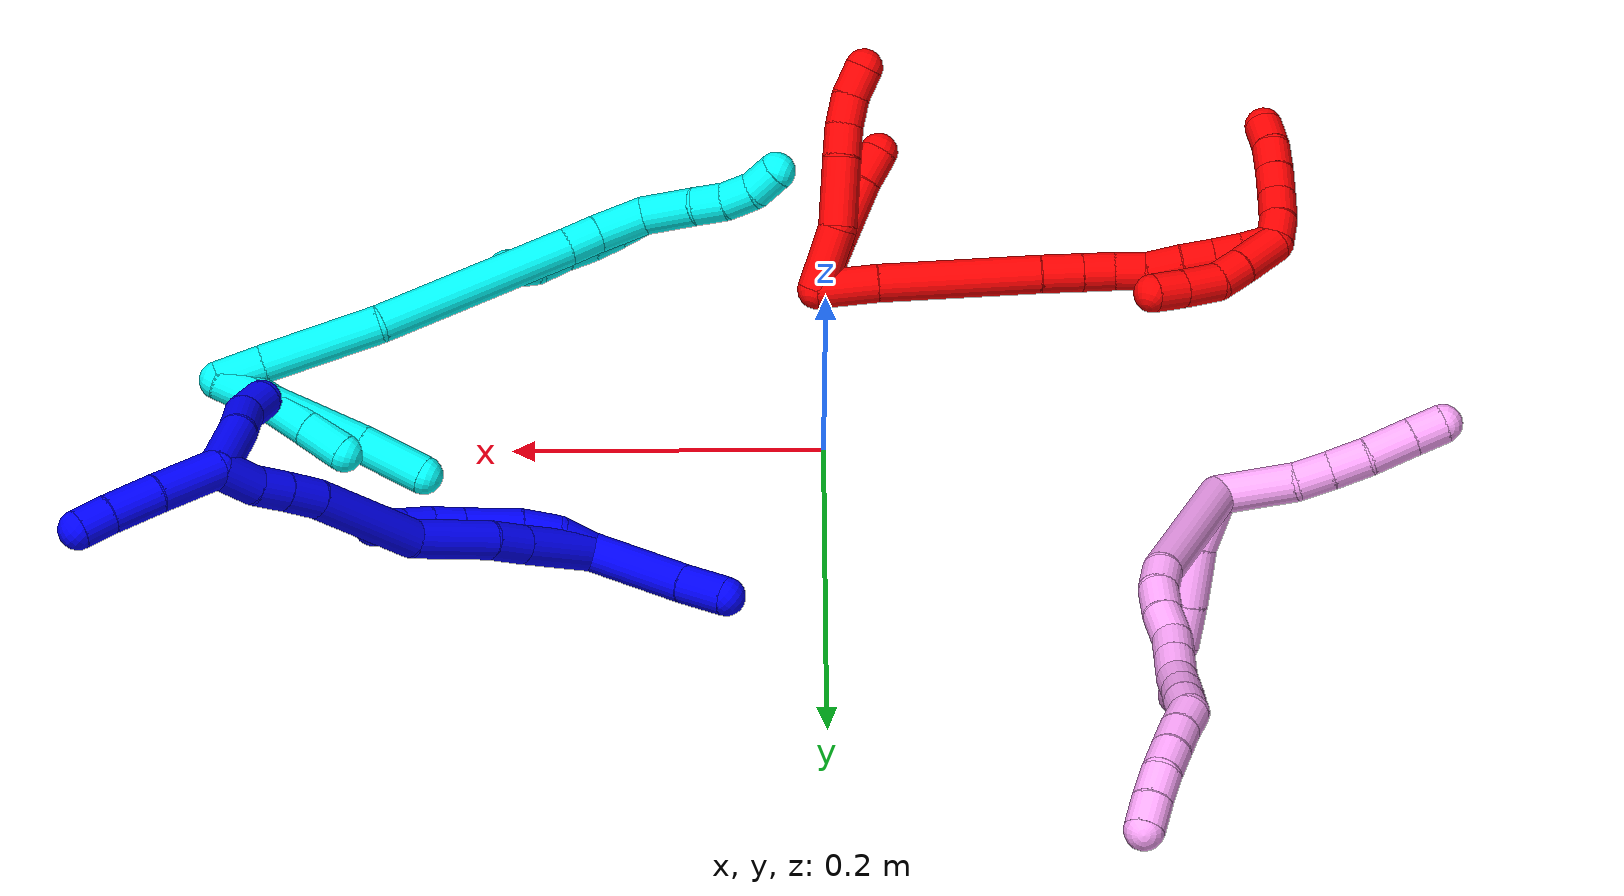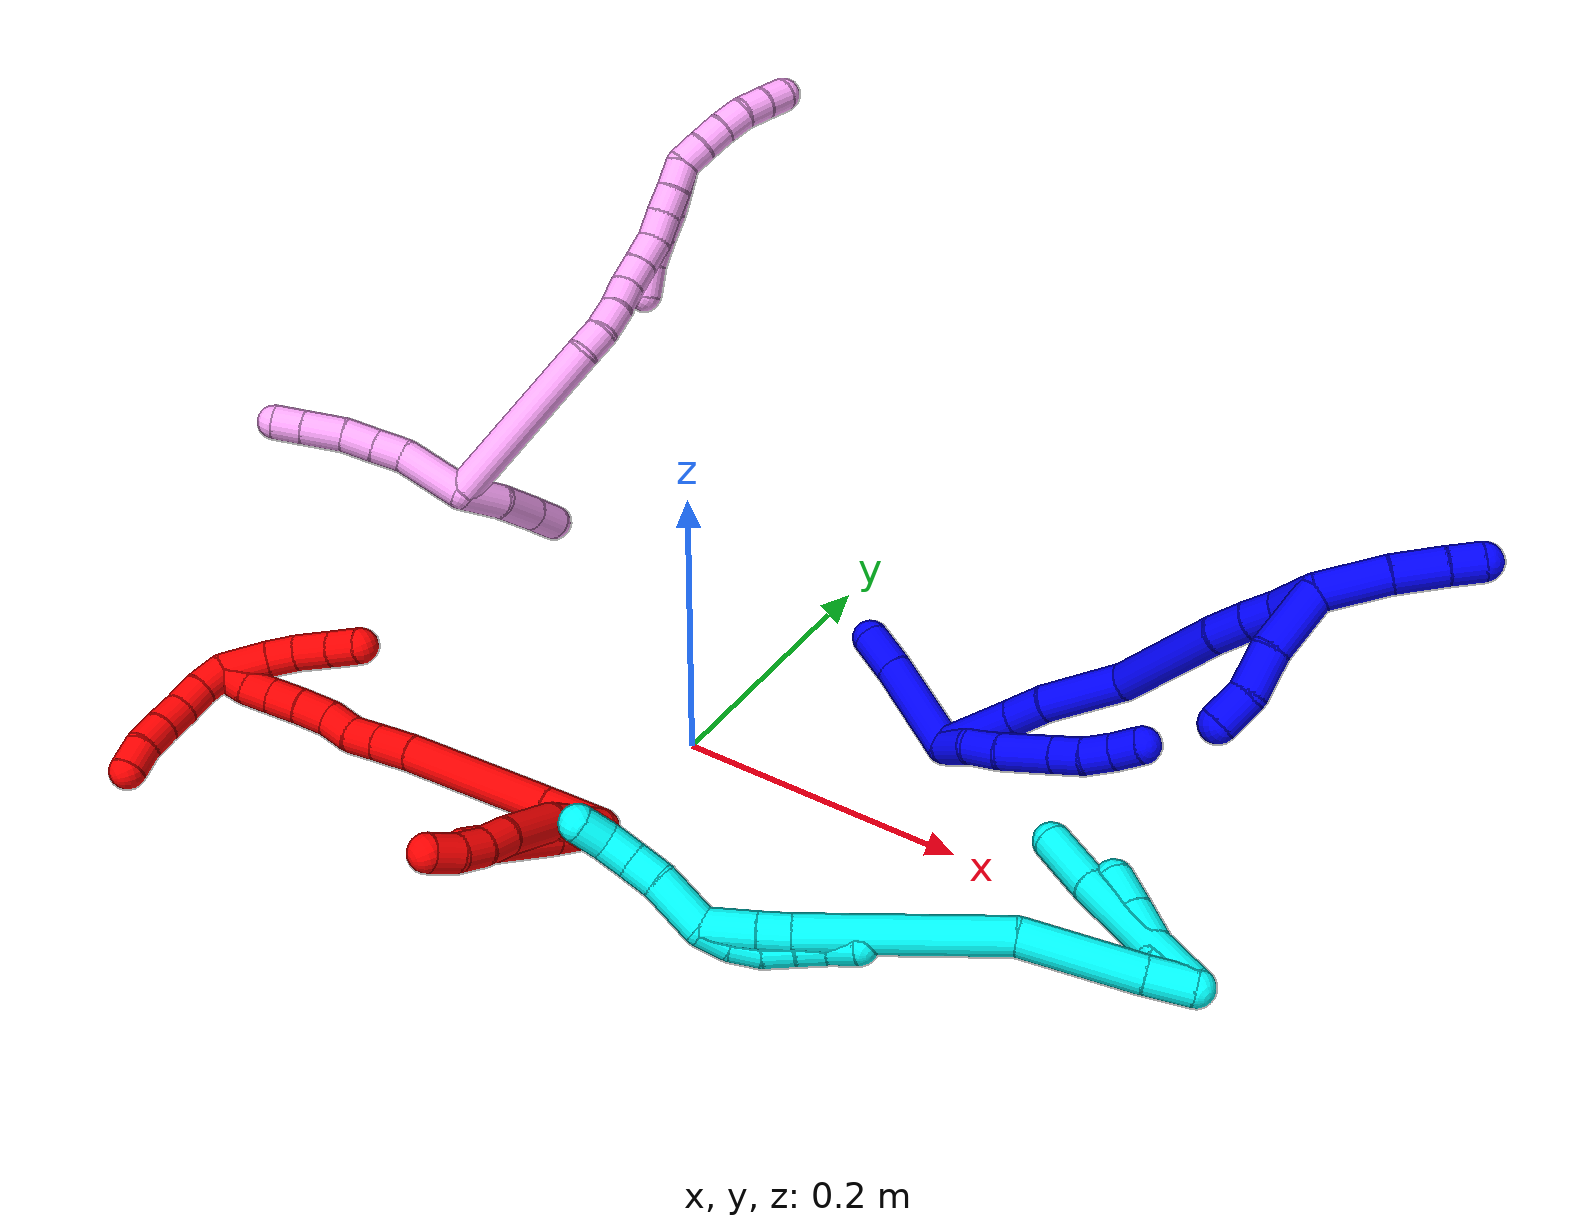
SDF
<sdf version="1.7">
 <world name="default">
  <plugin name="TubeGeneratorPlugin" filename="libtube_generator_plugin.so"/>
  <model name="photoneo_s_sensor">
   <static>1</static>
   <pose>0 0 2 1.57079 1.57079 3.14159</pose>
   <link name="link">
    <inertial><mass>0.1</mass></inertial>
    <sensor name="sensor" type="depth">
     <update_rate>30</update_rate>
     <camera>
      <horizontal_fov>1.22</horizontal_fov>
      <image><width>1920</width><height>1200</height><format>B8G8R8</format></image>
      <clip><near>0.1</near><far>4</far></clip>
      <depth_camera><output>points</output></depth_camera>
     </camera>
     <plugin name="camera_plugin" filename="libgazebo_ros_depth_camera.so">
      <baseline>0.2</baseline>
      <alwaysOn>1</alwaysOn>
      <updateRate>0.0</updateRate>
      <cameraName>camera_ir</cameraName>
      <imageTopicName>/camera/color/image_raw</imageTopicName>
      <cameraInfoTopicName>/camera/color/camera_info</cameraInfoTopicName>
      <depthImageTopicName>/camera/depth/image_raw</depthImageTopicName>
      <depthImageCameraInfoTopicName>/camera/depth/camera_info</depthImageCameraInfoTopicName>
      <pointCloudTopicName>/camera/depth/points</pointCloudTopicName>
      <frameName>fr_optical</frameName>
      <pointCloudCutoff>0.1</pointCloudCutoff>
      <pointCloudCutoffMax>2.0</pointCloudCutoffMax>
      <distortionK1>0</distortionK1>
      <distortionK2>0</distortionK2>
      <distortionK3>0</distortionK3>
      <distortionT1>0</distortionT1>
      <distortionT2>0</distortionT2>
      <CxPrime>0</CxPrime>
      <Cx>0</Cx>
      <Cy>0</Cy>
      <focalLength>0</focalLength>
      <hackBaseline>0</hackBaseline>
     </plugin>
    </sensor>
   </link>
  </model>
  <gravity>0 0 -9.8</gravity>
  <magnetic_field>6e-06 2.3e-05 -4.2e-05</magnetic_field>
  <atmosphere type="adiabatic"/>
  <physics name="default_physics" default="0" type="ode">
   <max_step_size>0.003</max_step_size>
   <real_time_factor>1</real_time_factor>
   <real_time_update_rate>1000</real_time_update_rate>
   <max_contacts>10000</max_contacts>
   <ode>
    <solver>
     <type>quick</type>
     <iters>100</iters>
     <sor>1.3</sor>
     <use_dynamic_moi_rescaling>0</use_dynamic_moi_rescaling>
    </solver>
    <constraints>
     <contact_max_correcting_vel>0</contact_max_correcting_vel>
     <contact_surface_layer>0.001</contact_surface_layer>
     <cfm>0</cfm>
     <erp>0.2</erp>
    </constraints>
   </ode>
  </physics>
  <scene><ambient>0.4 0.4 0.4 1</ambient><background>0.7 0.7 0.7 1</background><shadows>0</shadows></scene>
  <audio><device>default</device></audio>
  <spherical_coordinates>
   <surface_model>EARTH_WGS84</surface_model>
   <latitude_deg>0</latitude_deg>
   <longitude_deg>0</longitude_deg>
   <elevation>0</elevation>
   <heading_deg>0</heading_deg>
  </spherical_coordinates>
  <model name="bin">
   <static>1</static>
   <link name="bottom">
    <collision name="collision-bottom">
     <pose>0 0 -0.01 0 -0 0</pose>
     <geometry><box><size>0.8 0.6 0.02</size></box></geometry>
     <surface>
      <friction><ode><mu>100</mu><mu2>100</mu2></ode></friction>
      <contact><collide_bitmask>65535</collide_bitmask></contact>
     </surface>
    </collision>
   </link>
   <link name="west_wall">
    <collision name="collision-west_wall">
     <pose>-0.41 0 0.1 0 -0 0</pose>
     <geometry><box><size>0.02 0.6 0.2</size></box></geometry>
     <surface>
      <friction><ode><mu>100</mu><mu2>100</mu2></ode></friction>
      <contact><collide_bitmask>65535</collide_bitmask></contact>
     </surface>
    </collision>
   </link>
   <link name="east_wall">
    <collision name="collision-east_wall">
     <pose>0.41 0 0.1 0 -0 0</pose>
     <geometry><box><size>0.02 0.6 0.2</size></box></geometry>
     <surface>
      <friction><ode><mu>100</mu><mu2>100</mu2></ode></friction>
      <contact><collide_bitmask>65535</collide_bitmask></contact>
     </surface>
    </collision>
   </link>
   <link name="south_wall">
    <collision name="collision-south_wall">
     <pose>0 -0.31 0.1 0 -0 0</pose>
     <geometry><box><size>0.8 0.02 0.2</size></box></geometry>
     <surface>
      <friction><ode><mu>100</mu><mu2>100</mu2></ode></friction>
      <contact><collide_bitmask>65535</collide_bitmask></contact>
     </surface>
    </collision>
   </link>
   <link name="north_wall">
    <collision name="collision-north_wall">
     <pose>0 0.31 0.1 0 -0 0</pose>
     <geometry><box><size>0.8 0.02 0.2</size></box></geometry>
     <surface>
      <friction><ode><mu>100</mu><mu2>100</mu2></ode></friction>
      <contact><collide_bitmask>65535</collide_bitmask></contact>
     </surface>
    </collision>
   </link>
  </model>
  <model name="1">
   <static>0</static>
   <link name="1">
    <collision name="collision-cylinder-e_1_2_8">
     <pose>-0.000751 -0.003531 -0.012491 2.8661 -0.057766 -0.41094</pose>
     <geometry><cylinder><radius>0.0125</radius><length>0.026005</length></cylinder></geometry>
     <surface>
      <friction><ode><mu>1.16</mu><mu2>1.16</mu2><slip1>0</slip1><slip2>0</slip2></ode></friction>
      <contact><ode><kp>1e+06</kp><kd>1</kd><max_vel>0</max_vel><min_depth>0.001</min_depth></ode></contact>
     </surface>
    </collision>
    <visual name="visual-cylinder-e_1_2_8">
     <pose>-0.000751 -0.003531 -0.012491 2.8661 -0.057766 -0.41094</pose>
     <geometry><cylinder><radius>0.0125</radius><length>0.026005</length></cylinder></geometry>
     <material><ambient>0 0 1 1</ambient></material>
    </visual>
    <collision name="collision-cylinder-e_2_8_9">
     <pose>0.000203 -0.013168 -0.035561 2.6181 0.13867 0.507297</pose>
     <geometry><cylinder><radius>0.0125</radius><length>0.024664</length></cylinder></geometry>
     <surface>
      <friction><ode><mu>1.16</mu><mu2>1.16</mu2><slip1>0</slip1><slip2>0</slip2></ode></friction>
      <contact><ode><kp>1e+06</kp><kd>1</kd><max_vel>0</max_vel><min_depth>0.001</min_depth></ode></contact>
     </surface>
    </collision>
    <visual name="visual-cylinder-e_2_8_9">
     <pose>0.000203 -0.013168 -0.035561 2.6181 0.13867 0.507297</pose>
     <geometry><cylinder><radius>0.0125</radius><length>0.024664</length></cylinder></geometry>
     <material><ambient>0 0 1 1</ambient></material>
    </visual>
    <collision name="collision-cylinder-e_3_9_10">
     <pose>0.002963 -0.031369 -0.060692 2.44817 0.055726 0.153971</pose>
     <geometry><cylinder><radius>0.0125</radius><length>0.037906</length></cylinder></geometry>
     <surface>
      <friction><ode><mu>1.16</mu><mu2>1.16</mu2><slip1>0</slip1><slip2>0</slip2></ode></friction>
      <contact><ode><kp>1e+06</kp><kd>1</kd><max_vel>0</max_vel><min_depth>0.001</min_depth></ode></contact>
     </surface>
    </collision>
    <visual name="visual-cylinder-e_3_9_10">
     <pose>0.002963 -0.031369 -0.060692 2.44817 0.055726 0.153971</pose>
     <geometry><cylinder><radius>0.0125</radius><length>0.037906</length></cylinder></geometry>
     <material><ambient>0 0 1 1</ambient></material>
    </visual>
    <collision name="collision-cylinder-e_4_10_11">
     <pose>0.004492 -0.049854 -0.083383 2.47592 0.045662 0.131918</pose>
     <geometry><cylinder><radius>0.0125</radius><length>0.020714</length></cylinder></geometry>
     <surface>
      <friction><ode><mu>1.16</mu><mu2>1.16</mu2><slip1>0</slip1><slip2>0</slip2></ode></friction>
      <contact><ode><kp>1e+06</kp><kd>1</kd><max_vel>0</max_vel><min_depth>0.001</min_depth></ode></contact>
     </surface>
    </collision>
    <visual name="visual-cylinder-e_4_10_11">
     <pose>0.004492 -0.049854 -0.083383 2.47592 0.045662 0.131918</pose>
     <geometry><cylinder><radius>0.0125</radius><length>0.020714</length></cylinder></geometry>
     <material><ambient>0 0 1 1</ambient></material>
    </visual>
    <collision name="collision-cylinder-e_5_11_12">
     <pose>0.003633 -0.063397 -0.098863 2.36922 -0.129184 -0.315513</pose>
     <geometry><cylinder><radius>0.0125</radius><length>0.020674</length></cylinder></geometry>
     <surface>
      <friction><ode><mu>1.16</mu><mu2>1.16</mu2><slip1>0</slip1><slip2>0</slip2></ode></friction>
      <contact><ode><kp>1e+06</kp><kd>1</kd><max_vel>0</max_vel><min_depth>0.001</min_depth></ode></contact>
     </surface>
    </collision>
    <visual name="visual-cylinder-e_5_11_12">
     <pose>0.003633 -0.063397 -0.098863 2.36922 -0.129184 -0.315513</pose>
     <geometry><cylinder><radius>0.0125</radius><length>0.020674</length></cylinder></geometry>
     <material><ambient>0 0 1 1</ambient></material>
    </visual>
    <collision name="collision-cylinder-e_6_12_6">
     <pose>0.000164 -0.076534 -0.113951 2.48397 -0.214994 -0.612646</pose>
     <geometry><cylinder><radius>0.0125</radius><length>0.020036</length></cylinder></geometry>
     <surface>
      <friction><ode><mu>1.16</mu><mu2>1.16</mu2><slip1>0</slip1><slip2>0</slip2></ode></friction>
      <contact><ode><kp>1e+06</kp><kd>1</kd><max_vel>0</max_vel><min_depth>0.001</min_depth></ode></contact>
     </surface>
    </collision>
    <visual name="visual-cylinder-e_6_12_6">
     <pose>0.000164 -0.076534 -0.113951 2.48397 -0.214994 -0.612646</pose>
     <geometry><cylinder><radius>0.0125</radius><length>0.020036</length></cylinder></geometry>
     <material><ambient>0 0 1 1</ambient></material>
    </visual>
    <collision name="collision-cylinder-e_1_2_13">
     <pose>-0.0248 0.006392 0.023599 -0.26452 -0.792522 0.111208</pose>
     <geometry><cylinder><radius>0.0125</radius><length>0.069651</length></cylinder></geometry>
     <surface>
      <friction><ode><mu>1.16</mu><mu2>1.16</mu2><slip1>0</slip1><slip2>0</slip2></ode></friction>
      <contact><ode><kp>1e+06</kp><kd>1</kd><max_vel>0</max_vel><min_depth>0.001</min_depth></ode></contact>
     </surface>
    </collision>
    <visual name="visual-cylinder-e_1_2_13">
     <pose>-0.0248 0.006392 0.023599 -0.26452 -0.792522 0.111208</pose>
     <geometry><cylinder><radius>0.0125</radius><length>0.069651</length></cylinder></geometry>
     <material><ambient>0 0 1 1</ambient></material>
    </visual>
    <collision name="collision-cylinder-e_2_13_5">
     <pose>-0.06002 0.016344 0.057639 -0.328603 -0.756873 0.131651</pose>
     <geometry><cylinder><radius>0.0125</radius><length>0.030349</length></cylinder></geometry>
     <surface>
      <friction><ode><mu>1.16</mu><mu2>1.16</mu2><slip1>0</slip1><slip2>0</slip2></ode></friction>
      <contact><ode><kp>1e+06</kp><kd>1</kd><max_vel>0</max_vel><min_depth>0.001</min_depth></ode></contact>
     </surface>
    </collision>
    <visual name="visual-cylinder-e_2_13_5">
     <pose>-0.06002 0.016344 0.057639 -0.328603 -0.756873 0.131651</pose>
     <geometry><cylinder><radius>0.0125</radius><length>0.030349</length></cylinder></geometry>
     <material><ambient>0 0 1 1</ambient></material>
    </visual>
    <collision name="collision-cylinder-e_1_2_14">
     <pose>-0.009625 -0.015606 -0.021725 2.51866 -0.345393 -0.993071</pose>
     <geometry><cylinder><radius>0.0125</radius><length>0.056856</length></cylinder></geometry>
     <surface>
      <friction><ode><mu>1.16</mu><mu2>1.16</mu2><slip1>0</slip1><slip2>0</slip2></ode></friction>
      <contact><ode><kp>1e+06</kp><kd>1</kd><max_vel>0</max_vel><min_depth>0.001</min_depth></ode></contact>
     </surface>
    </collision>
    <visual name="visual-cylinder-e_1_2_14">
     <pose>-0.009625 -0.015606 -0.021725 2.51866 -0.345393 -0.993071</pose>
     <geometry><cylinder><radius>0.0125</radius><length>0.056856</length></cylinder></geometry>
     <material><ambient>0 0 1 1</ambient></material>
    </visual>
    <collision name="collision-cylinder-e_2_14_15">
     <pose>-0.02375 -0.038087 -0.053569 2.54484 -0.352481 -1.04973</pose>
     <geometry><cylinder><radius>0.0125</radius><length>0.02607</length></cylinder></geometry>
     <surface>
      <friction><ode><mu>1.16</mu><mu2>1.16</mu2><slip1>0</slip1><slip2>0</slip2></ode></friction>
      <contact><ode><kp>1e+06</kp><kd>1</kd><max_vel>0</max_vel><min_depth>0.001</min_depth></ode></contact>
     </surface>
    </collision>
    <visual name="visual-cylinder-e_2_14_15">
     <pose>-0.02375 -0.038087 -0.053569 2.54484 -0.352481 -1.04973</pose>
     <geometry><cylinder><radius>0.0125</radius><length>0.02607</length></cylinder></geometry>
     <material><ambient>0 0 1 1</ambient></material>
    </visual>
    <collision name="collision-cylinder-e_3_15_16">
     <pose>-0.034938 -0.062709 -0.08521 2.45204 -0.235305 -0.635929</pose>
     <geometry><cylinder><radius>0.0125</radius><length>0.057372</length></cylinder></geometry>
     <surface>
      <friction><ode><mu>1.16</mu><mu2>1.16</mu2><slip1>0</slip1><slip2>0</slip2></ode></friction>
      <contact><ode><kp>1e+06</kp><kd>1</kd><max_vel>0</max_vel><min_depth>0.001</min_depth></ode></contact>
     </surface>
    </collision>
    <visual name="visual-cylinder-e_3_15_16">
     <pose>-0.034938 -0.062709 -0.08521 2.45204 -0.235305 -0.635929</pose>
     <geometry><cylinder><radius>0.0125</radius><length>0.057372</length></cylinder></geometry>
     <material><ambient>0 0 1 1</ambient></material>
    </visual>
    <collision name="collision-cylinder-e_4_16_17">
     <pose>-0.057075 -0.094515 -0.141937 2.76164 -0.387003 -1.58963</pose>
     <geometry><cylinder><radius>0.0125</radius><length>0.08187</length></cylinder></geometry>
     <surface>
      <friction><ode><mu>1.16</mu><mu2>1.16</mu2><slip1>0</slip1><slip2>0</slip2></ode></friction>
      <contact><ode><kp>1e+06</kp><kd>1</kd><max_vel>0</max_vel><min_depth>0.001</min_depth></ode></contact>
     </surface>
    </collision>
    <visual name="visual-cylinder-e_4_16_17">
     <pose>-0.057075 -0.094515 -0.141937 2.76164 -0.387003 -1.58963</pose>
     <geometry><cylinder><radius>0.0125</radius><length>0.08187</length></cylinder></geometry>
     <material><ambient>0 0 1 1</ambient></material>
    </visual>
    <collision name="collision-cylinder-e_5_17_18">
     <pose>-0.076782 -0.114645 -0.187774 2.62282 -0.334654 -1.13367</pose>
     <geometry><cylinder><radius>0.0125</radius><length>0.025926</length></cylinder></geometry>
     <surface>
      <friction><ode><mu>1.16</mu><mu2>1.16</mu2><slip1>0</slip1><slip2>0</slip2></ode></friction>
      <contact><ode><kp>1e+06</kp><kd>1</kd><max_vel>0</max_vel><min_depth>0.001</min_depth></ode></contact>
     </surface>
    </collision>
    <visual name="visual-cylinder-e_5_17_18">
     <pose>-0.076782 -0.114645 -0.187774 2.62282 -0.334654 -1.13367</pose>
     <geometry><cylinder><radius>0.0125</radius><length>0.025926</length></cylinder></geometry>
     <material><ambient>0 0 1 1</ambient></material>
    </visual>
    <collision name="collision-cylinder-e_6_18_19">
     <pose>-0.084279 -0.126213 -0.207504 2.59802 -0.295779 -0.981857</pose>
     <geometry><cylinder><radius>0.0125</radius><length>0.022225</length></cylinder></geometry>
     <surface>
      <friction><ode><mu>1.16</mu><mu2>1.16</mu2><slip1>0</slip1><slip2>0</slip2></ode></friction>
      <contact><ode><kp>1e+06</kp><kd>1</kd><max_vel>0</max_vel><min_depth>0.001</min_depth></ode></contact>
     </surface>
    </collision>
    <visual name="visual-cylinder-e_6_18_19">
     <pose>-0.084279 -0.126213 -0.207504 2.59802 -0.295779 -0.981857</pose>
     <geometry><cylinder><radius>0.0125</radius><length>0.022225</length></cylinder></geometry>
     <material><ambient>0 0 1 1</ambient></material>
    </visual>
    <collision name="collision-cylinder-e_7_19_1">
     <pose>-0.092553 -0.136385 -0.229756 2.80015 -0.34616 -1.58478</pose>
     <geometry><cylinder><radius>0.0125</radius><length>0.029681</length></cylinder></geometry>
     <surface>
      <friction><ode><mu>1.16</mu><mu2>1.16</mu2><slip1>0</slip1><slip2>0</slip2></ode></friction>
      <contact><ode><kp>1e+06</kp><kd>1</kd><max_vel>0</max_vel><min_depth>0.001</min_depth></ode></contact>
     </surface>
    </collision>
    <visual name="visual-cylinder-e_7_19_1">
     <pose>-0.092553 -0.136385 -0.229756 2.80015 -0.34616 -1.58478</pose>
     <geometry><cylinder><radius>0.0125</radius><length>0.029681</length></cylinder></geometry>
     <material><ambient>0 0 1 1</ambient></material>
    </visual>
    <collision name="collision-cylinder-e_1_1_20">
     <pose>-0.101765 -0.160435 -0.253608 2.07524 -0.186532 -0.314356</pose>
     <geometry><cylinder><radius>0.0125</radius><length>0.045046</length></cylinder></geometry>
     <surface>
      <friction><ode><mu>1.16</mu><mu2>1.16</mu2><slip1>0</slip1><slip2>0</slip2></ode></friction>
      <contact><ode><kp>1e+06</kp><kd>1</kd><max_vel>0</max_vel><min_depth>0.001</min_depth></ode></contact>
     </surface>
    </collision>
    <visual name="visual-cylinder-e_1_1_20">
     <pose>-0.101765 -0.160435 -0.253608 2.07524 -0.186532 -0.314356</pose>
     <geometry><cylinder><radius>0.0125</radius><length>0.045046</length></cylinder></geometry>
     <material><ambient>0 0 1 1</ambient></material>
    </visual>
    <collision name="collision-cylinder-e_2_20_21">
     <pose>-0.107438 -0.194753 -0.271988 2.04575 -0.088799 -0.145352</pose>
     <geometry><cylinder><radius>0.0125</radius><length>0.033738</length></cylinder></geometry>
     <surface>
      <friction><ode><mu>1.16</mu><mu2>1.16</mu2><slip1>0</slip1><slip2>0</slip2></ode></friction>
      <contact><ode><kp>1e+06</kp><kd>1</kd><max_vel>0</max_vel><min_depth>0.001</min_depth></ode></contact>
     </surface>
    </collision>
    <visual name="visual-cylinder-e_2_20_21">
     <pose>-0.107438 -0.194753 -0.271988 2.04575 -0.088799 -0.145352</pose>
     <geometry><cylinder><radius>0.0125</radius><length>0.033738</length></cylinder></geometry>
     <material><ambient>0 0 1 1</ambient></material>
    </visual>
    <collision name="collision-cylinder-e_3_21_4">
     <pose>-0.109509 -0.219352 -0.284027 1.99451 -0.054255 -0.08396</pose>
     <geometry><cylinder><radius>0.0125</radius><length>0.021216</length></cylinder></geometry>
     <surface>
      <friction><ode><mu>1.16</mu><mu2>1.16</mu2><slip1>0</slip1><slip2>0</slip2></ode></friction>
      <contact><ode><kp>1e+06</kp><kd>1</kd><max_vel>0</max_vel><min_depth>0.001</min_depth></ode></contact>
     </surface>
    </collision>
    <visual name="visual-cylinder-e_3_21_4">
     <pose>-0.109509 -0.219352 -0.284027 1.99451 -0.054255 -0.08396</pose>
     <geometry><cylinder><radius>0.0125</radius><length>0.021216</length></cylinder></geometry>
     <material><ambient>0 0 1 1</ambient></material>
    </visual>
    <collision name="collision-cylinder-e_1_1_22">
     <pose>-0.081925 -0.125006 -0.241903 -1.50808 0.772095 -0.729297</pose>
     <geometry><cylinder><radius>0.0125</radius><length>0.044903</length></cylinder></geometry>
     <surface>
      <friction><ode><mu>1.16</mu><mu2>1.16</mu2><slip1>0</slip1><slip2>0</slip2></ode></friction>
      <contact><ode><kp>1e+06</kp><kd>1</kd><max_vel>0</max_vel><min_depth>0.001</min_depth></ode></contact>
     </surface>
    </collision>
    <visual name="visual-cylinder-e_1_1_22">
     <pose>-0.081925 -0.125006 -0.241903 -1.50808 0.772095 -0.729297</pose>
     <geometry><cylinder><radius>0.0125</radius><length>0.044903</length></cylinder></geometry>
     <material><ambient>0 0 1 1</ambient></material>
    </visual>
    <collision name="collision-cylinder-e_2_22_23">
     <pose>-0.053714 -0.100545 -0.240369 -1.50842 0.979587 -0.928678</pose>
     <geometry><cylinder><radius>0.0125</radius><length>0.030226</length></cylinder></geometry>
     <surface>
      <friction><ode><mu>1.16</mu><mu2>1.16</mu2><slip1>0</slip1><slip2>0</slip2></ode></friction>
      <contact><ode><kp>1e+06</kp><kd>1</kd><max_vel>0</max_vel><min_depth>0.001</min_depth></ode></contact>
     </surface>
    </collision>
    <visual name="visual-cylinder-e_2_22_23">
     <pose>-0.053714 -0.100545 -0.240369 -1.50842 0.979587 -0.928678</pose>
     <geometry><cylinder><radius>0.0125</radius><length>0.030226</length></cylinder></geometry>
     <material><ambient>0 0 1 1</ambient></material>
    </visual>
    <collision name="collision-cylinder-e_3_23_3">
     <pose>-0.033065 -0.083291 -0.236568 -1.21607 0.709604 -0.50471</pose>
     <geometry><cylinder><radius>0.0125</radius><length>0.024871</length></cylinder></geometry>
     <surface>
      <friction><ode><mu>1.16</mu><mu2>1.16</mu2><slip1>0</slip1><slip2>0</slip2></ode></friction>
      <contact><ode><kp>1e+06</kp><kd>1</kd><max_vel>0</max_vel><min_depth>0.001</min_depth></ode></contact>
     </surface>
    </collision>
    <visual name="visual-cylinder-e_3_23_3">
     <pose>-0.033065 -0.083291 -0.236568 -1.21607 0.709604 -0.50471</pose>
     <geometry><cylinder><radius>0.0125</radius><length>0.024871</length></cylinder></geometry>
     <material><ambient>0 0 1 1</ambient></material>
    </visual>
    <collision name="collision-sphere-3">
     <pose>-0.024962 -0.074445 -0.233291 0 -0 0</pose>
     <geometry><sphere><radius>0.0125</radius></sphere></geometry>
     <surface>
      <friction><ode><mu>1.16</mu><mu2>1.16</mu2><slip1>0</slip1><slip2>0</slip2></ode></friction>
      <contact><ode><kp>1e+06</kp><kd>1</kd><max_vel>0</max_vel><min_depth>0.001</min_depth></ode></contact>
     </surface>
    </collision>
    <visual name="visual-sphere-3">
     <pose>-0.024962 -0.074445 -0.233291 0 -0 0</pose>
     <geometry><sphere><radius>0.0125</radius></sphere></geometry>
     <material><ambient>0 0 1 1</ambient></material>
    </visual>
    <collision name="collision-sphere-23">
     <pose>-0.041167 -0.092138 -0.239844 0 -0 0</pose>
     <geometry><sphere><radius>0.0125</radius></sphere></geometry>
     <surface>
      <friction><ode><mu>1.16</mu><mu2>1.16</mu2><slip1>0</slip1><slip2>0</slip2></ode></friction>
      <contact><ode><kp>1e+06</kp><kd>1</kd><max_vel>0</max_vel><min_depth>0.001</min_depth></ode></contact>
     </surface>
    </collision>
    <visual name="visual-sphere-23">
     <pose>-0.041167 -0.092138 -0.239844 0 -0 0</pose>
     <geometry><sphere><radius>0.0125</radius></sphere></geometry>
     <material><ambient>0 0 1 1</ambient></material>
    </visual>
    <collision name="collision-sphere-22">
     <pose>-0.066262 -0.108952 -0.240894 0 -0 0</pose>
     <geometry><sphere><radius>0.0125</radius></sphere></geometry>
     <surface>
      <friction><ode><mu>1.16</mu><mu2>1.16</mu2><slip1>0</slip1><slip2>0</slip2></ode></friction>
      <contact><ode><kp>1e+06</kp><kd>1</kd><max_vel>0</max_vel><min_depth>0.001</min_depth></ode></contact>
     </surface>
    </collision>
    <visual name="visual-sphere-22">
     <pose>-0.066262 -0.108952 -0.240894 0 -0 0</pose>
     <geometry><sphere><radius>0.0125</radius></sphere></geometry>
     <material><ambient>0 0 1 1</ambient></material>
    </visual>
    <collision name="collision-sphere-4">
     <pose>-0.110085 -0.229008 -0.288382 0 -0 0</pose>
     <geometry><sphere><radius>0.0125</radius></sphere></geometry>
     <surface>
      <friction><ode><mu>1.16</mu><mu2>1.16</mu2><slip1>0</slip1><slip2>0</slip2></ode></friction>
      <contact><ode><kp>1e+06</kp><kd>1</kd><max_vel>0</max_vel><min_depth>0.001</min_depth></ode></contact>
     </surface>
    </collision>
    <visual name="visual-sphere-4">
     <pose>-0.110085 -0.229008 -0.288382 0 -0 0</pose>
     <geometry><sphere><radius>0.0125</radius></sphere></geometry>
     <material><ambient>0 0 1 1</ambient></material>
    </visual>
    <collision name="collision-sphere-21">
     <pose>-0.108934 -0.209696 -0.279672 0 -0 0</pose>
     <geometry><sphere><radius>0.0125</radius></sphere></geometry>
     <surface>
      <friction><ode><mu>1.16</mu><mu2>1.16</mu2><slip1>0</slip1><slip2>0</slip2></ode></friction>
      <contact><ode><kp>1e+06</kp><kd>1</kd><max_vel>0</max_vel><min_depth>0.001</min_depth></ode></contact>
     </surface>
    </collision>
    <visual name="visual-sphere-21">
     <pose>-0.108934 -0.209696 -0.279672 0 -0 0</pose>
     <geometry><sphere><radius>0.0125</radius></sphere></geometry>
     <material><ambient>0 0 1 1</ambient></material>
    </visual>
    <collision name="collision-sphere-20">
     <pose>-0.105942 -0.179811 -0.264305 0 -0 0</pose>
     <geometry><sphere><radius>0.0125</radius></sphere></geometry>
     <surface>
      <friction><ode><mu>1.16</mu><mu2>1.16</mu2><slip1>0</slip1><slip2>0</slip2></ode></friction>
      <contact><ode><kp>1e+06</kp><kd>1</kd><max_vel>0</max_vel><min_depth>0.001</min_depth></ode></contact>
     </surface>
    </collision>
    <visual name="visual-sphere-20">
     <pose>-0.105942 -0.179811 -0.264305 0 -0 0</pose>
     <geometry><sphere><radius>0.0125</radius></sphere></geometry>
     <material><ambient>0 0 1 1</ambient></material>
    </visual>
    <collision name="collision-sphere-12">
     <pose>0.002301 -0.070551 -0.106205 0 -0 0</pose>
     <geometry><sphere><radius>0.0125</radius></sphere></geometry>
     <surface>
      <friction><ode><mu>1.16</mu><mu2>1.16</mu2><slip1>0</slip1><slip2>0</slip2></ode></friction>
      <contact><ode><kp>1e+06</kp><kd>1</kd><max_vel>0</max_vel><min_depth>0.001</min_depth></ode></contact>
     </surface>
    </collision>
    <visual name="visual-sphere-12">
     <pose>0.002301 -0.070551 -0.106205 0 -0 0</pose>
     <geometry><sphere><radius>0.0125</radius></sphere></geometry>
     <material><ambient>0 0 1 1</ambient></material>
    </visual>
    <collision name="collision-sphere-11">
     <pose>0.004965 -0.056244 -0.09152 0 -0 0</pose>
     <geometry><sphere><radius>0.0125</radius></sphere></geometry>
     <surface>
      <friction><ode><mu>1.16</mu><mu2>1.16</mu2><slip1>0</slip1><slip2>0</slip2></ode></friction>
      <contact><ode><kp>1e+06</kp><kd>1</kd><max_vel>0</max_vel><min_depth>0.001</min_depth></ode></contact>
     </surface>
    </collision>
    <visual name="visual-sphere-11">
     <pose>0.004965 -0.056244 -0.09152 0 -0 0</pose>
     <geometry><sphere><radius>0.0125</radius></sphere></geometry>
     <material><ambient>0 0 1 1</ambient></material>
    </visual>
    <collision name="collision-sphere-10">
     <pose>0.004019 -0.043465 -0.075246 0 -0 0</pose>
     <geometry><sphere><radius>0.0125</radius></sphere></geometry>
     <surface>
      <friction><ode><mu>1.16</mu><mu2>1.16</mu2><slip1>0</slip1><slip2>0</slip2></ode></friction>
      <contact><ode><kp>1e+06</kp><kd>1</kd><max_vel>0</max_vel><min_depth>0.001</min_depth></ode></contact>
     </surface>
    </collision>
    <visual name="visual-sphere-10">
     <pose>0.004019 -0.043465 -0.075246 0 -0 0</pose>
     <geometry><sphere><radius>0.0125</radius></sphere></geometry>
     <material><ambient>0 0 1 1</ambient></material>
    </visual>
    <collision name="collision-sphere-9">
     <pose>0.001908 -0.019273 -0.046138 0 -0 0</pose>
     <geometry><sphere><radius>0.0125</radius></sphere></geometry>
     <surface>
      <friction><ode><mu>1.16</mu><mu2>1.16</mu2><slip1>0</slip1><slip2>0</slip2></ode></friction>
      <contact><ode><kp>1e+06</kp><kd>1</kd><max_vel>0</max_vel><min_depth>0.001</min_depth></ode></contact>
     </surface>
    </collision>
    <visual name="visual-sphere-9">
     <pose>0.001908 -0.019273 -0.046138 0 -0 0</pose>
     <geometry><sphere><radius>0.0125</radius></sphere></geometry>
     <material><ambient>0 0 1 1</ambient></material>
    </visual>
    <collision name="collision-sphere-2">
     <geometry><sphere><radius>0.0125</radius></sphere></geometry>
     <surface>
      <friction><ode><mu>1.16</mu><mu2>1.16</mu2><slip1>0</slip1><slip2>0</slip2></ode></friction>
      <contact><ode><kp>1e+06</kp><kd>1</kd><max_vel>0</max_vel><min_depth>0.001</min_depth></ode></contact>
     </surface>
    </collision>
    <visual name="visual-sphere-2">
     <geometry><sphere><radius>0.0125</radius></sphere></geometry>
     <material><ambient>0 0 1 1</ambient></material>
    </visual>
    <collision name="collision-sphere-19">
     <pose>-0.087518 -0.131711 -0.216602 0 -0 0</pose>
     <geometry><sphere><radius>0.0125</radius></sphere></geometry>
     <surface>
      <friction><ode><mu>1.16</mu><mu2>1.16</mu2><slip1>0</slip1><slip2>0</slip2></ode></friction>
      <contact><ode><kp>1e+06</kp><kd>1</kd><max_vel>0</max_vel><min_depth>0.001</min_depth></ode></contact>
     </surface>
    </collision>
    <visual name="visual-sphere-19">
     <pose>-0.087518 -0.131711 -0.216602 0 -0 0</pose>
     <geometry><sphere><radius>0.0125</radius></sphere></geometry>
     <material><ambient>0 0 1 1</ambient></material>
    </visual>
    <collision name="collision-sphere-8">
     <pose>-0.001501 -0.007062 -0.024983 0 -0 0</pose>
     <geometry><sphere><radius>0.0125</radius></sphere></geometry>
     <surface>
      <friction><ode><mu>1.16</mu><mu2>1.16</mu2><slip1>0</slip1><slip2>0</slip2></ode></friction>
      <contact><ode><kp>1e+06</kp><kd>1</kd><max_vel>0</max_vel><min_depth>0.001</min_depth></ode></contact>
     </surface>
    </collision>
    <visual name="visual-sphere-8">
     <pose>-0.001501 -0.007062 -0.024983 0 -0 0</pose>
     <geometry><sphere><radius>0.0125</radius></sphere></geometry>
     <material><ambient>0 0 1 1</ambient></material>
    </visual>
    <collision name="collision-sphere-6">
     <pose>-0.001973 -0.082516 -0.121698 0 -0 0</pose>
     <geometry><sphere><radius>0.0125</radius></sphere></geometry>
     <surface>
      <friction><ode><mu>1.16</mu><mu2>1.16</mu2><slip1>0</slip1><slip2>0</slip2></ode></friction>
      <contact><ode><kp>1e+06</kp><kd>1</kd><max_vel>0</max_vel><min_depth>0.001</min_depth></ode></contact>
     </surface>
    </collision>
    <visual name="visual-sphere-6">
     <pose>-0.001973 -0.082516 -0.121698 0 -0 0</pose>
     <geometry><sphere><radius>0.0125</radius></sphere></geometry>
     <material><ambient>0 0 1 1</ambient></material>
    </visual>
    <collision name="collision-sphere-13">
     <pose>-0.0496 0.012784 0.047198 0 -0 0</pose>
     <geometry><sphere><radius>0.0125</radius></sphere></geometry>
     <surface>
      <friction><ode><mu>1.16</mu><mu2>1.16</mu2><slip1>0</slip1><slip2>0</slip2></ode></friction>
      <contact><ode><kp>1e+06</kp><kd>1</kd><max_vel>0</max_vel><min_depth>0.001</min_depth></ode></contact>
     </surface>
    </collision>
    <visual name="visual-sphere-13">
     <pose>-0.0496 0.012784 0.047198 0 -0 0</pose>
     <geometry><sphere><radius>0.0125</radius></sphere></geometry>
     <material><ambient>0 0 1 1</ambient></material>
    </visual>
    <collision name="collision-sphere-5">
     <pose>-0.070439 0.019905 0.068081 0 -0 0</pose>
     <geometry><sphere><radius>0.0125</radius></sphere></geometry>
     <surface>
      <friction><ode><mu>1.16</mu><mu2>1.16</mu2><slip1>0</slip1><slip2>0</slip2></ode></friction>
      <contact><ode><kp>1e+06</kp><kd>1</kd><max_vel>0</max_vel><min_depth>0.001</min_depth></ode></contact>
     </surface>
    </collision>
    <visual name="visual-sphere-5">
     <pose>-0.070439 0.019905 0.068081 0 -0 0</pose>
     <geometry><sphere><radius>0.0125</radius></sphere></geometry>
     <material><ambient>0 0 1 1</ambient></material>
    </visual>
    <collision name="collision-sphere-14">
     <pose>-0.01925 -0.031212 -0.04345 0 -0 0</pose>
     <geometry><sphere><radius>0.0125</radius></sphere></geometry>
     <surface>
      <friction><ode><mu>1.16</mu><mu2>1.16</mu2><slip1>0</slip1><slip2>0</slip2></ode></friction>
      <contact><ode><kp>1e+06</kp><kd>1</kd><max_vel>0</max_vel><min_depth>0.001</min_depth></ode></contact>
     </surface>
    </collision>
    <visual name="visual-sphere-14">
     <pose>-0.01925 -0.031212 -0.04345 0 -0 0</pose>
     <geometry><sphere><radius>0.0125</radius></sphere></geometry>
     <material><ambient>0 0 1 1</ambient></material>
    </visual>
    <collision name="collision-sphere-15">
     <pose>-0.02825 -0.044962 -0.063688 0 -0 0</pose>
     <geometry><sphere><radius>0.0125</radius></sphere></geometry>
     <surface>
      <friction><ode><mu>1.16</mu><mu2>1.16</mu2><slip1>0</slip1><slip2>0</slip2></ode></friction>
      <contact><ode><kp>1e+06</kp><kd>1</kd><max_vel>0</max_vel><min_depth>0.001</min_depth></ode></contact>
     </surface>
    </collision>
    <visual name="visual-sphere-15">
     <pose>-0.02825 -0.044962 -0.063688 0 -0 0</pose>
     <geometry><sphere><radius>0.0125</radius></sphere></geometry>
     <material><ambient>0 0 1 1</ambient></material>
    </visual>
    <collision name="collision-sphere-16">
     <pose>-0.041625 -0.080455 -0.106732 0 -0 0</pose>
     <geometry><sphere><radius>0.0125</radius></sphere></geometry>
     <surface>
      <friction><ode><mu>1.16</mu><mu2>1.16</mu2><slip1>0</slip1><slip2>0</slip2></ode></friction>
      <contact><ode><kp>1e+06</kp><kd>1</kd><max_vel>0</max_vel><min_depth>0.001</min_depth></ode></contact>
     </surface>
    </collision>
    <visual name="visual-sphere-16">
     <pose>-0.041625 -0.080455 -0.106732 0 -0 0</pose>
     <geometry><sphere><radius>0.0125</radius></sphere></geometry>
     <material><ambient>0 0 1 1</ambient></material>
    </visual>
    <collision name="collision-sphere-17">
     <pose>-0.072525 -0.108574 -0.177141 0 -0 0</pose>
     <geometry><sphere><radius>0.0125</radius></sphere></geometry>
     <surface>
      <friction><ode><mu>1.16</mu><mu2>1.16</mu2><slip1>0</slip1><slip2>0</slip2></ode></friction>
      <contact><ode><kp>1e+06</kp><kd>1</kd><max_vel>0</max_vel><min_depth>0.001</min_depth></ode></contact>
     </surface>
    </collision>
    <visual name="visual-sphere-17">
     <pose>-0.072525 -0.108574 -0.177141 0 -0 0</pose>
     <geometry><sphere><radius>0.0125</radius></sphere></geometry>
     <material><ambient>0 0 1 1</ambient></material>
    </visual>
    <collision name="collision-sphere-18">
     <pose>-0.08104 -0.120715 -0.198407 0 -0 0</pose>
     <geometry><sphere><radius>0.0125</radius></sphere></geometry>
     <surface>
      <friction><ode><mu>1.16</mu><mu2>1.16</mu2><slip1>0</slip1><slip2>0</slip2></ode></friction>
      <contact><ode><kp>1e+06</kp><kd>1</kd><max_vel>0</max_vel><min_depth>0.001</min_depth></ode></contact>
     </surface>
    </collision>
    <visual name="visual-sphere-18">
     <pose>-0.08104 -0.120715 -0.198407 0 -0 0</pose>
     <geometry><sphere><radius>0.0125</radius></sphere></geometry>
     <material><ambient>0 0 1 1</ambient></material>
    </visual>
    <collision name="collision-sphere-1">
     <pose>-0.097588 -0.14106 -0.242911 0 -0 0</pose>
     <geometry><sphere><radius>0.0125</radius></sphere></geometry>
     <surface>
      <friction><ode><mu>1.16</mu><mu2>1.16</mu2><slip1>0</slip1><slip2>0</slip2></ode></friction>
      <contact><ode><kp>1e+06</kp><kd>1</kd><max_vel>0</max_vel><min_depth>0.001</min_depth></ode></contact>
     </surface>
    </collision>
    <visual name="visual-sphere-1">
     <pose>-0.097588 -0.14106 -0.242911 0 -0 0</pose>
     <geometry><sphere><radius>0.0125</radius></sphere></geometry>
     <material><ambient>0 0 1 1</ambient></material>
    </visual>
    <inertial>
     <pose>-0.045854 -0.075677 -0.122989 0 -0 0</pose>
     <mass>0.75</mass>
     <inertia><ixx>-9e-06</ixx><ixy>0</ixy><ixz>0</ixz><iyy>-8.7e-05</iyy><iyz>0</iyz><izz>6.9e-05</izz></inertia>
    </inertial>
   </link>
   <pose>0.148458 0.078553 0.0119 2.8843 0.988078 -0.877469</pose>
  </model>
  <model name="2">
   <static>0</static>
   <link name="2">
    <collision name="collision-cylinder-e_1_2_8">
     <pose>-8.3e-05 0.0117 0.017714 -0.58372 -0.003916 0.001176</pose>
     <geometry><cylinder><radius>0.0125</radius><length>0.042458</length></cylinder></geometry>
     <surface>
      <friction><ode><mu>1.16</mu><mu2>1.16</mu2><slip1>0</slip1><slip2>0</slip2></ode></friction>
      <contact><ode><kp>1e+06</kp><kd>1</kd><max_vel>0</max_vel><min_depth>0.001</min_depth></ode></contact>
     </surface>
    </collision>
    <visual name="visual-cylinder-e_1_2_8">
     <pose>-8.3e-05 0.0117 0.017714 -0.58372 -0.003916 0.001176</pose>
     <geometry><cylinder><radius>0.0125</radius><length>0.042458</length></cylinder></geometry>
     <material><ambient>1 0 0 1</ambient></material>
    </visual>
    <collision name="collision-cylinder-e_2_8_9">
     <pose>0.006099 0.032173 0.055275 -0.416208 0.281089 -0.059731</pose>
     <geometry><cylinder><radius>0.0125</radius><length>0.045172</length></cylinder></geometry>
     <surface>
      <friction><ode><mu>1.16</mu><mu2>1.16</mu2><slip1>0</slip1><slip2>0</slip2></ode></friction>
      <contact><ode><kp>1e+06</kp><kd>1</kd><max_vel>0</max_vel><min_depth>0.001</min_depth></ode></contact>
     </surface>
    </collision>
    <visual name="visual-cylinder-e_2_8_9">
     <pose>0.006099 0.032173 0.055275 -0.416208 0.281089 -0.059731</pose>
     <geometry><cylinder><radius>0.0125</radius><length>0.045172</length></cylinder></geometry>
     <material><ambient>1 0 0 1</ambient></material>
    </visual>
    <collision name="collision-cylinder-e_3_9_10">
     <pose>0.015244 0.043643 0.085024 -0.265947 0.273539 -0.036815</pose>
     <geometry><cylinder><radius>0.0125</radius><length>0.02132</length></cylinder></geometry>
     <surface>
      <friction><ode><mu>1.16</mu><mu2>1.16</mu2><slip1>0</slip1><slip2>0</slip2></ode></friction>
      <contact><ode><kp>1e+06</kp><kd>1</kd><max_vel>0</max_vel><min_depth>0.001</min_depth></ode></contact>
     </surface>
    </collision>
    <visual name="visual-cylinder-e_3_9_10">
     <pose>0.015244 0.043643 0.085024 -0.265947 0.273539 -0.036815</pose>
     <geometry><cylinder><radius>0.0125</radius><length>0.02132</length></cylinder></geometry>
     <material><ambient>1 0 0 1</ambient></material>
    </visual>
    <collision name="collision-cylinder-e_4_10_11">
     <pose>0.019493 0.049963 0.104359 -0.36669 0.134668 -0.025008</pose>
     <geometry><cylinder><radius>0.0125</radius><length>0.020392</length></cylinder></geometry>
     <surface>
      <friction><ode><mu>1.16</mu><mu2>1.16</mu2><slip1>0</slip1><slip2>0</slip2></ode></friction>
      <contact><ode><kp>1e+06</kp><kd>1</kd><max_vel>0</max_vel><min_depth>0.001</min_depth></ode></contact>
     </surface>
    </collision>
    <visual name="visual-cylinder-e_4_10_11">
     <pose>0.019493 0.049963 0.104359 -0.36669 0.134668 -0.025008</pose>
     <geometry><cylinder><radius>0.0125</radius><length>0.020392</length></cylinder></geometry>
     <material><ambient>1 0 0 1</ambient></material>
    </visual>
    <collision name="collision-cylinder-e_5_11_6">
     <pose>0.019875 0.058198 0.12298 -0.465196 -0.095683 0.022682</pose>
     <geometry><cylinder><radius>0.0125</radius><length>0.020658</length></cylinder></geometry>
     <surface>
      <friction><ode><mu>1.16</mu><mu2>1.16</mu2><slip1>0</slip1><slip2>0</slip2></ode></friction>
      <contact><ode><kp>1e+06</kp><kd>1</kd><max_vel>0</max_vel><min_depth>0.001</min_depth></ode></contact>
     </surface>
    </collision>
    <visual name="visual-cylinder-e_5_11_6">
     <pose>0.019875 0.058198 0.12298 -0.465196 -0.095683 0.022682</pose>
     <geometry><cylinder><radius>0.0125</radius><length>0.020658</length></cylinder></geometry>
     <material><ambient>1 0 0 1</ambient></material>
    </visual>
    <collision name="collision-cylinder-e_1_2_12">
     <pose>-0.000697 0.005271 0.017167 -0.297934 -0.038781 0.005821</pose>
     <geometry><cylinder><radius>0.0125</radius><length>0.035943</length></cylinder></geometry>
     <surface>
      <friction><ode><mu>1.16</mu><mu2>1.16</mu2><slip1>0</slip1><slip2>0</slip2></ode></friction>
      <contact><ode><kp>1e+06</kp><kd>1</kd><max_vel>0</max_vel><min_depth>0.001</min_depth></ode></contact>
     </surface>
    </collision>
    <visual name="visual-cylinder-e_1_2_12">
     <pose>-0.000697 0.005271 0.017167 -0.297934 -0.038781 0.005821</pose>
     <geometry><cylinder><radius>0.0125</radius><length>0.035943</length></cylinder></geometry>
     <material><ambient>1 0 0 1</ambient></material>
    </visual>
    <collision name="collision-cylinder-e_2_12_13">
     <pose>-0.002527 0.017598 0.054017 -0.344181 -0.054176 0.009419</pose>
     <geometry><cylinder><radius>0.0125</radius><length>0.041882</length></cylinder></geometry>
     <surface>
      <friction><ode><mu>1.16</mu><mu2>1.16</mu2><slip1>0</slip1><slip2>0</slip2></ode></friction>
      <contact><ode><kp>1e+06</kp><kd>1</kd><max_vel>0</max_vel><min_depth>0.001</min_depth></ode></contact>
     </surface>
    </collision>
    <visual name="visual-cylinder-e_2_12_13">
     <pose>-0.002527 0.017598 0.054017 -0.344181 -0.054176 0.009419</pose>
     <geometry><cylinder><radius>0.0125</radius><length>0.041882</length></cylinder></geometry>
     <material><ambient>1 0 0 1</ambient></material>
    </visual>
    <collision name="collision-cylinder-e_3_13_5">
     <pose>-0.005388 0.027463 0.084287 -0.259398 -0.156338 0.020432</pose>
     <geometry><cylinder><radius>0.0125</radius><length>0.022176</length></cylinder></geometry>
     <surface>
      <friction><ode><mu>1.16</mu><mu2>1.16</mu2><slip1>0</slip1><slip2>0</slip2></ode></friction>
      <contact><ode><kp>1e+06</kp><kd>1</kd><max_vel>0</max_vel><min_depth>0.001</min_depth></ode></contact>
     </surface>
    </collision>
    <visual name="visual-cylinder-e_3_13_5">
     <pose>-0.005388 0.027463 0.084287 -0.259398 -0.156338 0.020432</pose>
     <geometry><cylinder><radius>0.0125</radius><length>0.022176</length></cylinder></geometry>
     <material><ambient>1 0 0 1</ambient></material>
    </visual>
    <collision name="collision-cylinder-e_1_2_14">
     <pose>-0.018083 0.002274 0.008449 -0.262916 -1.12016 0.165442</pose>
     <geometry><cylinder><radius>0.0125</radius><length>0.040177</length></cylinder></geometry>
     <surface>
      <friction><ode><mu>1.16</mu><mu2>1.16</mu2><slip1>0</slip1><slip2>0</slip2></ode></friction>
      <contact><ode><kp>1e+06</kp><kd>1</kd><max_vel>0</max_vel><min_depth>0.001</min_depth></ode></contact>
     </surface>
    </collision>
    <visual name="visual-cylinder-e_1_2_14">
     <pose>-0.018083 0.002274 0.008449 -0.262916 -1.12016 0.165442</pose>
     <geometry><cylinder><radius>0.0125</radius><length>0.040177</length></cylinder></geometry>
     <material><ambient>1 0 0 1</ambient></material>
    </visual>
    <collision name="collision-cylinder-e_2_14_15">
     <pose>-0.084476 0.008248 0.037621 -0.176706 -1.15985 0.115926</pose>
     <geometry><cylinder><radius>0.0125</radius><length>0.105394</length></cylinder></geometry>
     <surface>
      <friction><ode><mu>1.16</mu><mu2>1.16</mu2><slip1>0</slip1><slip2>0</slip2></ode></friction>
      <contact><ode><kp>1e+06</kp><kd>1</kd><max_vel>0</max_vel><min_depth>0.001</min_depth></ode></contact>
     </surface>
    </collision>
    <visual name="visual-cylinder-e_2_14_15">
     <pose>-0.084476 0.008248 0.037621 -0.176706 -1.15985 0.115926</pose>
     <geometry><cylinder><radius>0.0125</radius><length>0.105394</length></cylinder></geometry>
     <material><ambient>1 0 0 1</ambient></material>
    </visual>
    <collision name="collision-cylinder-e_3_15_16">
     <pose>-0.145138 0.012047 0.063849 -0.017745 -1.1515 0.011518</pose>
     <geometry><cylinder><radius>0.0125</radius><length>0.027048</length></cylinder></geometry>
     <surface>
      <friction><ode><mu>1.16</mu><mu2>1.16</mu2><slip1>0</slip1><slip2>0</slip2></ode></friction>
      <contact><ode><kp>1e+06</kp><kd>1</kd><max_vel>0</max_vel><min_depth>0.001</min_depth></ode></contact>
     </surface>
    </collision>
    <visual name="visual-cylinder-e_3_15_16">
     <pose>-0.145138 0.012047 0.063849 -0.017745 -1.1515 0.011518</pose>
     <geometry><cylinder><radius>0.0125</radius><length>0.027048</length></cylinder></geometry>
     <material><ambient>1 0 0 1</ambient></material>
    </visual>
    <collision name="collision-cylinder-e_4_16_17">
     <pose>-0.167402 0.01212 0.073854 0.005518 -1.14465 -0.003555</pose>
     <geometry><cylinder><radius>0.0125</radius><length>0.021771</length></cylinder></geometry>
     <surface>
      <friction><ode><mu>1.16</mu><mu2>1.16</mu2><slip1>0</slip1><slip2>0</slip2></ode></friction>
      <contact><ode><kp>1e+06</kp><kd>1</kd><max_vel>0</max_vel><min_depth>0.001</min_depth></ode></contact>
     </surface>
    </collision>
    <visual name="visual-cylinder-e_4_16_17">
     <pose>-0.167402 0.01212 0.073854 0.005518 -1.14465 -0.003555</pose>
     <geometry><cylinder><radius>0.0125</radius><length>0.021771</length></cylinder></geometry>
     <material><ambient>1 0 0 1</ambient></material>
    </visual>
    <collision name="collision-cylinder-e_5_17_18">
     <pose>-0.187278 0.01442 0.080906 -0.738722 -1.23723 0.537782</pose>
     <geometry><cylinder><radius>0.0125</radius><length>0.02109</length></cylinder></geometry>
     <surface>
      <friction><ode><mu>1.16</mu><mu2>1.16</mu2><slip1>0</slip1><slip2>0</slip2></ode></friction>
      <contact><ode><kp>1e+06</kp><kd>1</kd><max_vel>0</max_vel><min_depth>0.001</min_depth></ode></contact>
     </surface>
    </collision>
    <visual name="visual-cylinder-e_5_17_18">
     <pose>-0.187278 0.01442 0.080906 -0.738722 -1.23723 0.537782</pose>
     <geometry><cylinder><radius>0.0125</radius><length>0.02109</length></cylinder></geometry>
     <material><ambient>1 0 0 1</ambient></material>
    </visual>
    <collision name="collision-cylinder-e_6_18_19">
     <pose>-0.206999 0.019237 0.089056 -0.418979 -1.01008 0.234013</pose>
     <geometry><cylinder><radius>0.0125</radius><length>0.023043</length></cylinder></geometry>
     <surface>
      <friction><ode><mu>1.16</mu><mu2>1.16</mu2><slip1>0</slip1><slip2>0</slip2></ode></friction>
      <contact><ode><kp>1e+06</kp><kd>1</kd><max_vel>0</max_vel><min_depth>0.001</min_depth></ode></contact>
     </surface>
    </collision>
    <visual name="visual-cylinder-e_6_18_19">
     <pose>-0.206999 0.019237 0.089056 -0.418979 -1.01008 0.234013</pose>
     <geometry><cylinder><radius>0.0125</radius><length>0.023043</length></cylinder></geometry>
     <material><ambient>1 0 0 1</ambient></material>
    </visual>
    <collision name="collision-cylinder-e_7_19_20">
     <pose>-0.22593 0.023225 0.099707 -0.287645 -1.04933 0.167247</pose>
     <geometry><cylinder><radius>0.0125</radius><length>0.021161</length></cylinder></geometry>
     <surface>
      <friction><ode><mu>1.16</mu><mu2>1.16</mu2><slip1>0</slip1><slip2>0</slip2></ode></friction>
      <contact><ode><kp>1e+06</kp><kd>1</kd><max_vel>0</max_vel><min_depth>0.001</min_depth></ode></contact>
     </surface>
    </collision>
    <visual name="visual-cylinder-e_7_19_20">
     <pose>-0.22593 0.023225 0.099707 -0.287645 -1.04933 0.167247</pose>
     <geometry><cylinder><radius>0.0125</radius><length>0.021161</length></cylinder></geometry>
     <material><ambient>1 0 0 1</ambient></material>
    </visual>
    <collision name="collision-cylinder-e_8_20_21">
     <pose>-0.243767 0.026364 0.109743 -0.318707 -1.02623 0.18062</pose>
     <geometry><cylinder><radius>0.0125</radius><length>0.020256</length></cylinder></geometry>
     <surface>
      <friction><ode><mu>1.16</mu><mu2>1.16</mu2><slip1>0</slip1><slip2>0</slip2></ode></friction>
      <contact><ode><kp>1e+06</kp><kd>1</kd><max_vel>0</max_vel><min_depth>0.001</min_depth></ode></contact>
     </surface>
    </collision>
    <visual name="visual-cylinder-e_8_20_21">
     <pose>-0.243767 0.026364 0.109743 -0.318707 -1.02623 0.18062</pose>
     <geometry><cylinder><radius>0.0125</radius><length>0.020256</length></cylinder></geometry>
     <material><ambient>1 0 0 1</ambient></material>
    </visual>
    <collision name="collision-cylinder-e_9_21_1">
     <pose>-0.260692 0.031867 0.118905 -0.745646 -0.967861 0.405503</pose>
     <geometry><cylinder><radius>0.0125</radius><length>0.020061</length></cylinder></geometry>
     <surface>
      <friction><ode><mu>1.16</mu><mu2>1.16</mu2><slip1>0</slip1><slip2>0</slip2></ode></friction>
      <contact><ode><kp>1e+06</kp><kd>1</kd><max_vel>0</max_vel><min_depth>0.001</min_depth></ode></contact>
     </surface>
    </collision>
    <visual name="visual-cylinder-e_9_21_1">
     <pose>-0.260692 0.031867 0.118905 -0.745646 -0.967861 0.405503</pose>
     <geometry><cylinder><radius>0.0125</radius><length>0.020061</length></cylinder></geometry>
     <material><ambient>1 0 0 1</ambient></material>
    </visual>
    <collision name="collision-cylinder-e_1_1_22">
     <pose>-0.261566 0.038276 0.109091 -2.96132 0.479092 -2.43272</pose>
     <geometry><cylinder><radius>0.0125</radius><length>0.032053</length></cylinder></geometry>
     <surface>
      <friction><ode><mu>1.16</mu><mu2>1.16</mu2><slip1>0</slip1><slip2>0</slip2></ode></friction>
      <contact><ode><kp>1e+06</kp><kd>1</kd><max_vel>0</max_vel><min_depth>0.001</min_depth></ode></contact>
     </surface>
    </collision>
    <visual name="visual-cylinder-e_1_1_22">
     <pose>-0.261566 0.038276 0.109091 -2.96132 0.479092 -2.43272</pose>
     <geometry><cylinder><radius>0.0125</radius><length>0.032053</length></cylinder></geometry>
     <material><ambient>1 0 0 1</ambient></material>
    </visual>
    <collision name="collision-cylinder-e_2_22_23">
     <pose>-0.249025 0.042019 0.086501 -3.00373 0.535728 -2.64872</pose>
     <geometry><cylinder><radius>0.0125</radius><length>0.02019</length></cylinder></geometry>
     <surface>
      <friction><ode><mu>1.16</mu><mu2>1.16</mu2><slip1>0</slip1><slip2>0</slip2></ode></friction>
      <contact><ode><kp>1e+06</kp><kd>1</kd><max_vel>0</max_vel><min_depth>0.001</min_depth></ode></contact>
     </surface>
    </collision>
    <visual name="visual-cylinder-e_2_22_23">
     <pose>-0.249025 0.042019 0.086501 -3.00373 0.535728 -2.64872</pose>
     <geometry><cylinder><radius>0.0125</radius><length>0.02019</length></cylinder></geometry>
     <material><ambient>1 0 0 1</ambient></material>
    </visual>
    <collision name="collision-cylinder-e_3_23_24">
     <pose>-0.233997 0.046036 0.069467 -2.81859 0.837473 -2.43977</pose>
     <geometry><cylinder><radius>0.0125</radius><length>0.026582</length></cylinder></geometry>
     <surface>
      <friction><ode><mu>1.16</mu><mu2>1.16</mu2><slip1>0</slip1><slip2>0</slip2></ode></friction>
      <contact><ode><kp>1e+06</kp><kd>1</kd><max_vel>0</max_vel><min_depth>0.001</min_depth></ode></contact>
     </surface>
    </collision>
    <visual name="visual-cylinder-e_3_23_24">
     <pose>-0.233997 0.046036 0.069467 -2.81859 0.837473 -2.43977</pose>
     <geometry><cylinder><radius>0.0125</radius><length>0.026582</length></cylinder></geometry>
     <material><ambient>1 0 0 1</ambient></material>
    </visual>
    <collision name="collision-cylinder-e_4_24_4">
     <pose>-0.216116 0.051424 0.054595 -2.76234 0.857513 -2.34655</pose>
     <geometry><cylinder><radius>0.0125</radius><length>0.021175</length></cylinder></geometry>
     <surface>
      <friction><ode><mu>1.16</mu><mu2>1.16</mu2><slip1>0</slip1><slip2>0</slip2></ode></friction>
      <contact><ode><kp>1e+06</kp><kd>1</kd><max_vel>0</max_vel><min_depth>0.001</min_depth></ode></contact>
     </surface>
    </collision>
    <visual name="visual-cylinder-e_4_24_4">
     <pose>-0.216116 0.051424 0.054595 -2.76234 0.857513 -2.34655</pose>
     <geometry><cylinder><radius>0.0125</radius><length>0.021175</length></cylinder></geometry>
     <material><ambient>1 0 0 1</ambient></material>
    </visual>
    <collision name="collision-cylinder-e_1_1_25">
     <pose>-0.267363 0.034024 0.132808 0.173242 0.15979 0.013905</pose>
     <geometry><cylinder><radius>0.0125</radius><length>0.02</length></cylinder></geometry>
     <surface>
      <friction><ode><mu>1.16</mu><mu2>1.16</mu2><slip1>0</slip1><slip2>0</slip2></ode></friction>
      <contact><ode><kp>1e+06</kp><kd>1</kd><max_vel>0</max_vel><min_depth>0.001</min_depth></ode></contact>
     </surface>
    </collision>
    <visual name="visual-cylinder-e_1_1_25">
     <pose>-0.267363 0.034024 0.132808 0.173242 0.15979 0.013905</pose>
     <geometry><cylinder><radius>0.0125</radius><length>0.02</length></cylinder></geometry>
     <material><ambient>1 0 0 1</ambient></material>
    </visual>
    <collision name="collision-cylinder-e_2_25_26">
     <pose>-0.262542 0.030204 0.151757 0.225797 0.328839 0.037619</pose>
     <geometry><cylinder><radius>0.0125</radius><length>0.02</length></cylinder></geometry>
     <surface>
      <friction><ode><mu>1.16</mu><mu2>1.16</mu2><slip1>0</slip1><slip2>0</slip2></ode></friction>
      <contact><ode><kp>1e+06</kp><kd>1</kd><max_vel>0</max_vel><min_depth>0.001</min_depth></ode></contact>
     </surface>
    </collision>
    <visual name="visual-cylinder-e_2_25_26">
     <pose>-0.262542 0.030204 0.151757 0.225797 0.328839 0.037619</pose>
     <geometry><cylinder><radius>0.0125</radius><length>0.02</length></cylinder></geometry>
     <material><ambient>1 0 0 1</ambient></material>
    </visual>
    <collision name="collision-cylinder-e_3_26_27">
     <pose>-0.255657 0.027195 0.170246 0.095762 0.37418 0.018142</pose>
     <geometry><cylinder><radius>0.0125</radius><length>0.02</length></cylinder></geometry>
     <surface>
      <friction><ode><mu>1.16</mu><mu2>1.16</mu2><slip1>0</slip1><slip2>0</slip2></ode></friction>
      <contact><ode><kp>1e+06</kp><kd>1</kd><max_vel>0</max_vel><min_depth>0.001</min_depth></ode></contact>
     </surface>
    </collision>
    <visual name="visual-cylinder-e_3_26_27">
     <pose>-0.255657 0.027195 0.170246 0.095762 0.37418 0.018142</pose>
     <geometry><cylinder><radius>0.0125</radius><length>0.02</length></cylinder></geometry>
     <material><ambient>1 0 0 1</ambient></material>
    </visual>
    <collision name="collision-cylinder-e_4_27_28">
     <pose>-0.248009 0.025129 0.188604 0.128636 0.410819 0.026837</pose>
     <geometry><cylinder><radius>0.0125</radius><length>0.02</length></cylinder></geometry>
     <surface>
      <friction><ode><mu>1.16</mu><mu2>1.16</mu2><slip1>0</slip1><slip2>0</slip2></ode></friction>
      <contact><ode><kp>1e+06</kp><kd>1</kd><max_vel>0</max_vel><min_depth>0.001</min_depth></ode></contact>
     </surface>
    </collision>
    <visual name="visual-cylinder-e_4_27_28">
     <pose>-0.248009 0.025129 0.188604 0.128636 0.410819 0.026837</pose>
     <geometry><cylinder><radius>0.0125</radius><length>0.02</length></cylinder></geometry>
     <material><ambient>1 0 0 1</ambient></material>
    </visual>
    <collision name="collision-cylinder-e_5_28_3">
     <pose>-0.239164 0.021133 0.205974 0.328261 0.506441 0.085664</pose>
     <geometry><cylinder><radius>0.0125</radius><length>0.02</length></cylinder></geometry>
     <surface>
      <friction><ode><mu>1.16</mu><mu2>1.16</mu2><slip1>0</slip1><slip2>0</slip2></ode></friction>
      <contact><ode><kp>1e+06</kp><kd>1</kd><max_vel>0</max_vel><min_depth>0.001</min_depth></ode></contact>
     </surface>
    </collision>
    <visual name="visual-cylinder-e_5_28_3">
     <pose>-0.239164 0.021133 0.205974 0.328261 0.506441 0.085664</pose>
     <geometry><cylinder><radius>0.0125</radius><length>0.02</length></cylinder></geometry>
     <material><ambient>1 0 0 1</ambient></material>
    </visual>
    <collision name="collision-sphere-3">
     <pose>-0.234314 0.018314 0.214252 0 -0 0</pose>
     <geometry><sphere><radius>0.0125</radius></sphere></geometry>
     <surface>
      <friction><ode><mu>1.16</mu><mu2>1.16</mu2><slip1>0</slip1><slip2>0</slip2></ode></friction>
      <contact><ode><kp>1e+06</kp><kd>1</kd><max_vel>0</max_vel><min_depth>0.001</min_depth></ode></contact>
     </surface>
    </collision>
    <visual name="visual-sphere-3">
     <pose>-0.234314 0.018314 0.214252 0 -0 0</pose>
     <geometry><sphere><radius>0.0125</radius></sphere></geometry>
     <material><ambient>1 0 0 1</ambient></material>
    </visual>
    <collision name="collision-sphere-28">
     <pose>-0.244015 0.023953 0.197696 0 -0 0</pose>
     <geometry><sphere><radius>0.0125</radius></sphere></geometry>
     <surface>
      <friction><ode><mu>1.16</mu><mu2>1.16</mu2><slip1>0</slip1><slip2>0</slip2></ode></friction>
      <contact><ode><kp>1e+06</kp><kd>1</kd><max_vel>0</max_vel><min_depth>0.001</min_depth></ode></contact>
     </surface>
    </collision>
    <visual name="visual-sphere-28">
     <pose>-0.244015 0.023953 0.197696 0 -0 0</pose>
     <geometry><sphere><radius>0.0125</radius></sphere></geometry>
     <material><ambient>1 0 0 1</ambient></material>
    </visual>
    <collision name="collision-sphere-27">
     <pose>-0.252002 0.026305 0.179512 0 -0 0</pose>
     <geometry><sphere><radius>0.0125</radius></sphere></geometry>
     <surface>
      <friction><ode><mu>1.16</mu><mu2>1.16</mu2><slip1>0</slip1><slip2>0</slip2></ode></friction>
      <contact><ode><kp>1e+06</kp><kd>1</kd><max_vel>0</max_vel><min_depth>0.001</min_depth></ode></contact>
     </surface>
    </collision>
    <visual name="visual-sphere-27">
     <pose>-0.252002 0.026305 0.179512 0 -0 0</pose>
     <geometry><sphere><radius>0.0125</radius></sphere></geometry>
     <material><ambient>1 0 0 1</ambient></material>
    </visual>
    <collision name="collision-sphere-26">
     <pose>-0.259313 0.028085 0.160981 0 -0 0</pose>
     <geometry><sphere><radius>0.0125</radius></sphere></geometry>
     <surface>
      <friction><ode><mu>1.16</mu><mu2>1.16</mu2><slip1>0</slip1><slip2>0</slip2></ode></friction>
      <contact><ode><kp>1e+06</kp><kd>1</kd><max_vel>0</max_vel><min_depth>0.001</min_depth></ode></contact>
     </surface>
    </collision>
    <visual name="visual-sphere-26">
     <pose>-0.259313 0.028085 0.160981 0 -0 0</pose>
     <geometry><sphere><radius>0.0125</radius></sphere></geometry>
     <material><ambient>1 0 0 1</ambient></material>
    </visual>
    <collision name="collision-sphere-25">
     <pose>-0.265771 0.032322 0.142533 0 -0 0</pose>
     <geometry><sphere><radius>0.0125</radius></sphere></geometry>
     <surface>
      <friction><ode><mu>1.16</mu><mu2>1.16</mu2><slip1>0</slip1><slip2>0</slip2></ode></friction>
      <contact><ode><kp>1e+06</kp><kd>1</kd><max_vel>0</max_vel><min_depth>0.001</min_depth></ode></contact>
     </surface>
    </collision>
    <visual name="visual-sphere-25">
     <pose>-0.265771 0.032322 0.142533 0 -0 0</pose>
     <geometry><sphere><radius>0.0125</radius></sphere></geometry>
     <material><ambient>1 0 0 1</ambient></material>
    </visual>
    <collision name="collision-sphere-4">
     <pose>-0.20811 0.053989 0.04816 0 -0 0</pose>
     <geometry><sphere><radius>0.0125</radius></sphere></geometry>
     <surface>
      <friction><ode><mu>1.16</mu><mu2>1.16</mu2><slip1>0</slip1><slip2>0</slip2></ode></friction>
      <contact><ode><kp>1e+06</kp><kd>1</kd><max_vel>0</max_vel><min_depth>0.001</min_depth></ode></contact>
     </surface>
    </collision>
    <visual name="visual-sphere-4">
     <pose>-0.20811 0.053989 0.04816 0 -0 0</pose>
     <geometry><sphere><radius>0.0125</radius></sphere></geometry>
     <material><ambient>1 0 0 1</ambient></material>
    </visual>
    <collision name="collision-sphere-24">
     <pose>-0.224122 0.04886 0.061031 0 -0 0</pose>
     <geometry><sphere><radius>0.0125</radius></sphere></geometry>
     <surface>
      <friction><ode><mu>1.16</mu><mu2>1.16</mu2><slip1>0</slip1><slip2>0</slip2></ode></friction>
      <contact><ode><kp>1e+06</kp><kd>1</kd><max_vel>0</max_vel><min_depth>0.001</min_depth></ode></contact>
     </surface>
    </collision>
    <visual name="visual-sphere-24">
     <pose>-0.224122 0.04886 0.061031 0 -0 0</pose>
     <geometry><sphere><radius>0.0125</radius></sphere></geometry>
     <material><ambient>1 0 0 1</ambient></material>
    </visual>
    <collision name="collision-sphere-23">
     <pose>-0.243872 0.043212 0.077903 0 -0 0</pose>
     <geometry><sphere><radius>0.0125</radius></sphere></geometry>
     <surface>
      <friction><ode><mu>1.16</mu><mu2>1.16</mu2><slip1>0</slip1><slip2>0</slip2></ode></friction>
      <contact><ode><kp>1e+06</kp><kd>1</kd><max_vel>0</max_vel><min_depth>0.001</min_depth></ode></contact>
     </surface>
    </collision>
    <visual name="visual-sphere-23">
     <pose>-0.243872 0.043212 0.077903 0 -0 0</pose>
     <geometry><sphere><radius>0.0125</radius></sphere></geometry>
     <material><ambient>1 0 0 1</ambient></material>
    </visual>
    <collision name="collision-sphere-22">
     <pose>-0.254178 0.040826 0.0951 0 -0 0</pose>
     <geometry><sphere><radius>0.0125</radius></sphere></geometry>
     <surface>
      <friction><ode><mu>1.16</mu><mu2>1.16</mu2><slip1>0</slip1><slip2>0</slip2></ode></friction>
      <contact><ode><kp>1e+06</kp><kd>1</kd><max_vel>0</max_vel><min_depth>0.001</min_depth></ode></contact>
     </surface>
    </collision>
    <visual name="visual-sphere-22">
     <pose>-0.254178 0.040826 0.0951 0 -0 0</pose>
     <geometry><sphere><radius>0.0125</radius></sphere></geometry>
     <material><ambient>1 0 0 1</ambient></material>
    </visual>
    <collision name="collision-sphere-1">
     <pose>-0.268954 0.035726 0.123083 0 -0 0</pose>
     <geometry><sphere><radius>0.0125</radius></sphere></geometry>
     <surface>
      <friction><ode><mu>1.16</mu><mu2>1.16</mu2><slip1>0</slip1><slip2>0</slip2></ode></friction>
      <contact><ode><kp>1e+06</kp><kd>1</kd><max_vel>0</max_vel><min_depth>0.001</min_depth></ode></contact>
     </surface>
    </collision>
    <visual name="visual-sphere-1">
     <pose>-0.268954 0.035726 0.123083 0 -0 0</pose>
     <geometry><sphere><radius>0.0125</radius></sphere></geometry>
     <material><ambient>1 0 0 1</ambient></material>
    </visual>
    <collision name="collision-sphere-21">
     <pose>-0.25243 0.028008 0.114726 0 -0 0</pose>
     <geometry><sphere><radius>0.0125</radius></sphere></geometry>
     <surface>
      <friction><ode><mu>1.16</mu><mu2>1.16</mu2><slip1>0</slip1><slip2>0</slip2></ode></friction>
      <contact><ode><kp>1e+06</kp><kd>1</kd><max_vel>0</max_vel><min_depth>0.001</min_depth></ode></contact>
     </surface>
    </collision>
    <visual name="visual-sphere-21">
     <pose>-0.25243 0.028008 0.114726 0 -0 0</pose>
     <geometry><sphere><radius>0.0125</radius></sphere></geometry>
     <material><ambient>1 0 0 1</ambient></material>
    </visual>
    <collision name="collision-sphere-6">
     <pose>0.018888 0.062811 0.13217 0 -0 0</pose>
     <geometry><sphere><radius>0.0125</radius></sphere></geometry>
     <surface>
      <friction><ode><mu>1.16</mu><mu2>1.16</mu2><slip1>0</slip1><slip2>0</slip2></ode></friction>
      <contact><ode><kp>1e+06</kp><kd>1</kd><max_vel>0</max_vel><min_depth>0.001</min_depth></ode></contact>
     </surface>
    </collision>
    <visual name="visual-sphere-6">
     <pose>0.018888 0.062811 0.13217 0 -0 0</pose>
     <geometry><sphere><radius>0.0125</radius></sphere></geometry>
     <material><ambient>1 0 0 1</ambient></material>
    </visual>
    <collision name="collision-sphere-11">
     <pose>0.020862 0.053586 0.113791 0 -0 0</pose>
     <geometry><sphere><radius>0.0125</radius></sphere></geometry>
     <surface>
      <friction><ode><mu>1.16</mu><mu2>1.16</mu2><slip1>0</slip1><slip2>0</slip2></ode></friction>
      <contact><ode><kp>1e+06</kp><kd>1</kd><max_vel>0</max_vel><min_depth>0.001</min_depth></ode></contact>
     </surface>
    </collision>
    <visual name="visual-sphere-11">
     <pose>0.020862 0.053586 0.113791 0 -0 0</pose>
     <geometry><sphere><radius>0.0125</radius></sphere></geometry>
     <material><ambient>1 0 0 1</ambient></material>
    </visual>
    <collision name="collision-sphere-10">
     <pose>0.018124 0.046341 0.094927 0 -0 0</pose>
     <geometry><sphere><radius>0.0125</radius></sphere></geometry>
     <surface>
      <friction><ode><mu>1.16</mu><mu2>1.16</mu2><slip1>0</slip1><slip2>0</slip2></ode></friction>
      <contact><ode><kp>1e+06</kp><kd>1</kd><max_vel>0</max_vel><min_depth>0.001</min_depth></ode></contact>
     </surface>
    </collision>
    <visual name="visual-sphere-10">
     <pose>0.018124 0.046341 0.094927 0 -0 0</pose>
     <geometry><sphere><radius>0.0125</radius></sphere></geometry>
     <material><ambient>1 0 0 1</ambient></material>
    </visual>
    <collision name="collision-sphere-9">
     <pose>0.012365 0.040946 0.075122 0 -0 0</pose>
     <geometry><sphere><radius>0.0125</radius></sphere></geometry>
     <surface>
      <friction><ode><mu>1.16</mu><mu2>1.16</mu2><slip1>0</slip1><slip2>0</slip2></ode></friction>
      <contact><ode><kp>1e+06</kp><kd>1</kd><max_vel>0</max_vel><min_depth>0.001</min_depth></ode></contact>
     </surface>
    </collision>
    <visual name="visual-sphere-9">
     <pose>0.012365 0.040946 0.075122 0 -0 0</pose>
     <geometry><sphere><radius>0.0125</radius></sphere></geometry>
     <material><ambient>1 0 0 1</ambient></material>
    </visual>
    <collision name="collision-sphere-2">
     <geometry><sphere><radius>0.0125</radius></sphere></geometry>
     <surface>
      <friction><ode><mu>1.16</mu><mu2>1.16</mu2><slip1>0</slip1><slip2>0</slip2></ode></friction>
      <contact><ode><kp>1e+06</kp><kd>1</kd><max_vel>0</max_vel><min_depth>0.001</min_depth></ode></contact>
     </surface>
    </collision>
    <visual name="visual-sphere-2">
     <geometry><sphere><radius>0.0125</radius></sphere></geometry>
     <material><ambient>1 0 0 1</ambient></material>
    </visual>
    <collision name="collision-sphere-19">
     <pose>-0.216756 0.02173 0.094653 0 -0 0</pose>
     <geometry><sphere><radius>0.0125</radius></sphere></geometry>
     <surface>
      <friction><ode><mu>1.16</mu><mu2>1.16</mu2><slip1>0</slip1><slip2>0</slip2></ode></friction>
      <contact><ode><kp>1e+06</kp><kd>1</kd><max_vel>0</max_vel><min_depth>0.001</min_depth></ode></contact>
     </surface>
    </collision>
    <visual name="visual-sphere-19">
     <pose>-0.216756 0.02173 0.094653 0 -0 0</pose>
     <geometry><sphere><radius>0.0125</radius></sphere></geometry>
     <material><ambient>1 0 0 1</ambient></material>
    </visual>
    <collision name="collision-sphere-8">
     <pose>-0.000166 0.0234 0.035428 0 -0 0</pose>
     <geometry><sphere><radius>0.0125</radius></sphere></geometry>
     <surface>
      <friction><ode><mu>1.16</mu><mu2>1.16</mu2><slip1>0</slip1><slip2>0</slip2></ode></friction>
      <contact><ode><kp>1e+06</kp><kd>1</kd><max_vel>0</max_vel><min_depth>0.001</min_depth></ode></contact>
     </surface>
    </collision>
    <visual name="visual-sphere-8">
     <pose>-0.000166 0.0234 0.035428 0 -0 0</pose>
     <geometry><sphere><radius>0.0125</radius></sphere></geometry>
     <material><ambient>1 0 0 1</ambient></material>
    </visual>
    <collision name="collision-sphere-12">
     <pose>-0.001394 0.010543 0.034333 0 -0 0</pose>
     <geometry><sphere><radius>0.0125</radius></sphere></geometry>
     <surface>
      <friction><ode><mu>1.16</mu><mu2>1.16</mu2><slip1>0</slip1><slip2>0</slip2></ode></friction>
      <contact><ode><kp>1e+06</kp><kd>1</kd><max_vel>0</max_vel><min_depth>0.001</min_depth></ode></contact>
     </surface>
    </collision>
    <visual name="visual-sphere-12">
     <pose>-0.001394 0.010543 0.034333 0 -0 0</pose>
     <geometry><sphere><radius>0.0125</radius></sphere></geometry>
     <material><ambient>1 0 0 1</ambient></material>
    </visual>
    <collision name="collision-sphere-13">
     <pose>-0.003661 0.024654 0.073701 0 -0 0</pose>
     <geometry><sphere><radius>0.0125</radius></sphere></geometry>
     <surface>
      <friction><ode><mu>1.16</mu><mu2>1.16</mu2><slip1>0</slip1><slip2>0</slip2></ode></friction>
      <contact><ode><kp>1e+06</kp><kd>1</kd><max_vel>0</max_vel><min_depth>0.001</min_depth></ode></contact>
     </surface>
    </collision>
    <visual name="visual-sphere-13">
     <pose>-0.003661 0.024654 0.073701 0 -0 0</pose>
     <geometry><sphere><radius>0.0125</radius></sphere></geometry>
     <material><ambient>1 0 0 1</ambient></material>
    </visual>
    <collision name="collision-sphere-5">
     <pose>-0.007114 0.030273 0.094873 0 -0 0</pose>
     <geometry><sphere><radius>0.0125</radius></sphere></geometry>
     <surface>
      <friction><ode><mu>1.16</mu><mu2>1.16</mu2><slip1>0</slip1><slip2>0</slip2></ode></friction>
      <contact><ode><kp>1e+06</kp><kd>1</kd><max_vel>0</max_vel><min_depth>0.001</min_depth></ode></contact>
     </surface>
    </collision>
    <visual name="visual-sphere-5">
     <pose>-0.007114 0.030273 0.094873 0 -0 0</pose>
     <geometry><sphere><radius>0.0125</radius></sphere></geometry>
     <material><ambient>1 0 0 1</ambient></material>
    </visual>
    <collision name="collision-sphere-14">
     <pose>-0.036167 0.004548 0.016898 0 -0 0</pose>
     <geometry><sphere><radius>0.0125</radius></sphere></geometry>
     <surface>
      <friction><ode><mu>1.16</mu><mu2>1.16</mu2><slip1>0</slip1><slip2>0</slip2></ode></friction>
      <contact><ode><kp>1e+06</kp><kd>1</kd><max_vel>0</max_vel><min_depth>0.001</min_depth></ode></contact>
     </surface>
    </collision>
    <visual name="visual-sphere-14">
     <pose>-0.036167 0.004548 0.016898 0 -0 0</pose>
     <geometry><sphere><radius>0.0125</radius></sphere></geometry>
     <material><ambient>1 0 0 1</ambient></material>
    </visual>
    <collision name="collision-sphere-15">
     <pose>-0.132786 0.011949 0.058344 0 -0 0</pose>
     <geometry><sphere><radius>0.0125</radius></sphere></geometry>
     <surface>
      <friction><ode><mu>1.16</mu><mu2>1.16</mu2><slip1>0</slip1><slip2>0</slip2></ode></friction>
      <contact><ode><kp>1e+06</kp><kd>1</kd><max_vel>0</max_vel><min_depth>0.001</min_depth></ode></contact>
     </surface>
    </collision>
    <visual name="visual-sphere-15">
     <pose>-0.132786 0.011949 0.058344 0 -0 0</pose>
     <geometry><sphere><radius>0.0125</radius></sphere></geometry>
     <material><ambient>1 0 0 1</ambient></material>
    </visual>
    <collision name="collision-sphere-16">
     <pose>-0.15749 0.012144 0.069354 0 -0 0</pose>
     <geometry><sphere><radius>0.0125</radius></sphere></geometry>
     <surface>
      <friction><ode><mu>1.16</mu><mu2>1.16</mu2><slip1>0</slip1><slip2>0</slip2></ode></friction>
      <contact><ode><kp>1e+06</kp><kd>1</kd><max_vel>0</max_vel><min_depth>0.001</min_depth></ode></contact>
     </surface>
    </collision>
    <visual name="visual-sphere-16">
     <pose>-0.15749 0.012144 0.069354 0 -0 0</pose>
     <geometry><sphere><radius>0.0125</radius></sphere></geometry>
     <material><ambient>1 0 0 1</ambient></material>
    </visual>
    <collision name="collision-sphere-17">
     <pose>-0.177314 0.012095 0.078353 0 -0 0</pose>
     <geometry><sphere><radius>0.0125</radius></sphere></geometry>
     <surface>
      <friction><ode><mu>1.16</mu><mu2>1.16</mu2><slip1>0</slip1><slip2>0</slip2></ode></friction>
      <contact><ode><kp>1e+06</kp><kd>1</kd><max_vel>0</max_vel><min_depth>0.001</min_depth></ode></contact>
     </surface>
    </collision>
    <visual name="visual-sphere-17">
     <pose>-0.177314 0.012095 0.078353 0 -0 0</pose>
     <geometry><sphere><radius>0.0125</radius></sphere></geometry>
     <material><ambient>1 0 0 1</ambient></material>
    </visual>
    <collision name="collision-sphere-18">
     <pose>-0.197241 0.016744 0.083458 0 -0 0</pose>
     <geometry><sphere><radius>0.0125</radius></sphere></geometry>
     <surface>
      <friction><ode><mu>1.16</mu><mu2>1.16</mu2><slip1>0</slip1><slip2>0</slip2></ode></friction>
      <contact><ode><kp>1e+06</kp><kd>1</kd><max_vel>0</max_vel><min_depth>0.001</min_depth></ode></contact>
     </surface>
    </collision>
    <visual name="visual-sphere-18">
     <pose>-0.197241 0.016744 0.083458 0 -0 0</pose>
     <geometry><sphere><radius>0.0125</radius></sphere></geometry>
     <material><ambient>1 0 0 1</ambient></material>
    </visual>
    <collision name="collision-sphere-20">
     <pose>-0.235104 0.02472 0.104761 0 -0 0</pose>
     <geometry><sphere><radius>0.0125</radius></sphere></geometry>
     <surface>
      <friction><ode><mu>1.16</mu><mu2>1.16</mu2><slip1>0</slip1><slip2>0</slip2></ode></friction>
      <contact><ode><kp>1e+06</kp><kd>1</kd><max_vel>0</max_vel><min_depth>0.001</min_depth></ode></contact>
     </surface>
    </collision>
    <visual name="visual-sphere-20">
     <pose>-0.235104 0.02472 0.104761 0 -0 0</pose>
     <geometry><sphere><radius>0.0125</radius></sphere></geometry>
     <material><ambient>1 0 0 1</ambient></material>
    </visual>
    <inertial>
     <pose>-0.119168 0.023655 0.077104 0 -0 0</pose>
     <mass>0.75</mass>
     <inertia>
      <ixx>7.5e-05</ixx>
      <ixy>0</ixy>
      <ixz>0</ixz>
      <iyy>0.000181</iyy>
      <iyz>0</iyz>
      <izz>0.000104</izz>
     </inertia>
    </inertial>
   </link>
   <pose>0.003689 -0.111128 0.012384 1.58936 -0.064912 -0.350666</pose>
  </model>
  <model name="3">
   <static>0</static>
   <link name="3">
    <collision name="collision-cylinder-e_1_2_8">
     <pose>-0.000834 0.003546 -0.052122 -3.07367 -0.01596 0.461416</pose>
     <geometry><cylinder><radius>0.0125</radius><length>0.104499</length></cylinder></geometry>
     <surface>
      <friction><ode><mu>1.16</mu><mu2>1.16</mu2><slip1>0</slip1><slip2>0</slip2></ode></friction>
      <contact><ode><kp>1e+06</kp><kd>1</kd><max_vel>0</max_vel><min_depth>0.001</min_depth></ode></contact>
     </surface>
    </collision>
    <visual name="visual-cylinder-e_1_2_8">
     <pose>-0.000834 0.003546 -0.052122 -3.07367 -0.01596 0.461416</pose>
     <geometry><cylinder><radius>0.0125</radius><length>0.104499</length></cylinder></geometry>
     <material><ambient>0.003922 1 0.996078 1</ambient></material>
    </visual>
    <collision name="collision-cylinder-e_2_8_6">
     <pose>-0.002144 0.010178 -0.12678 -3.00549 -0.020954 0.30505</pose>
     <geometry><cylinder><radius>0.0125</radius><length>0.045501</length></cylinder></geometry>
     <surface>
      <friction><ode><mu>1.16</mu><mu2>1.16</mu2><slip1>0</slip1><slip2>0</slip2></ode></friction>
      <contact><ode><kp>1e+06</kp><kd>1</kd><max_vel>0</max_vel><min_depth>0.001</min_depth></ode></contact>
     </surface>
    </collision>
    <visual name="visual-cylinder-e_2_8_6">
     <pose>-0.002144 0.010178 -0.12678 -3.00549 -0.020954 0.30505</pose>
     <geometry><cylinder><radius>0.0125</radius><length>0.045501</length></cylinder></geometry>
     <material><ambient>0.003922 1 0.996078 1</ambient></material>
    </visual>
    <collision name="collision-cylinder-e_1_2_9">
     <pose>5.4e-05 5.6e-05 -0.015838 -3.13806 0.003434 -1.5422</pose>
     <geometry><cylinder><radius>0.0125</radius><length>0.031676</length></cylinder></geometry>
     <surface>
      <friction><ode><mu>1.16</mu><mu2>1.16</mu2><slip1>0</slip1><slip2>0</slip2></ode></friction>
      <contact><ode><kp>1e+06</kp><kd>1</kd><max_vel>0</max_vel><min_depth>0.001</min_depth></ode></contact>
     </surface>
    </collision>
    <visual name="visual-cylinder-e_1_2_9">
     <pose>5.4e-05 5.6e-05 -0.015838 -3.13806 0.003434 -1.5422</pose>
     <geometry><cylinder><radius>0.0125</radius><length>0.031676</length></cylinder></geometry>
     <material><ambient>0.003922 1 0.996078 1</ambient></material>
    </visual>
    <collision name="collision-cylinder-e_2_9_10">
     <pose>-0.000848 0.005886 -0.05007 -2.83742 -0.049562 0.320656</pose>
     <geometry><cylinder><radius>0.0125</radius><length>0.038607</length></cylinder></geometry>
     <surface>
      <friction><ode><mu>1.16</mu><mu2>1.16</mu2><slip1>0</slip1><slip2>0</slip2></ode></friction>
      <contact><ode><kp>1e+06</kp><kd>1</kd><max_vel>0</max_vel><min_depth>0.001</min_depth></ode></contact>
     </surface>
    </collision>
    <visual name="visual-cylinder-e_2_9_10">
     <pose>-0.000848 0.005886 -0.05007 -2.83742 -0.049562 0.320656</pose>
     <geometry><cylinder><radius>0.0125</radius><length>0.038607</length></cylinder></geometry>
     <material><ambient>0.003922 1 0.996078 1</ambient></material>
    </visual>
    <collision name="collision-cylinder-e_3_10_5">
     <pose>-0.002158 0.016009 -0.082669 -2.84452 -0.023833 0.15894</pose>
     <geometry><cylinder><radius>0.0125</radius><length>0.029717</length></cylinder></geometry>
     <surface>
      <friction><ode><mu>1.16</mu><mu2>1.16</mu2><slip1>0</slip1><slip2>0</slip2></ode></friction>
      <contact><ode><kp>1e+06</kp><kd>1</kd><max_vel>0</max_vel><min_depth>0.001</min_depth></ode></contact>
     </surface>
    </collision>
    <visual name="visual-cylinder-e_3_10_5">
     <pose>-0.002158 0.016009 -0.082669 -2.84452 -0.023833 0.15894</pose>
     <geometry><cylinder><radius>0.0125</radius><length>0.029717</length></cylinder></geometry>
     <material><ambient>0.003922 1 0.996078 1</ambient></material>
    </visual>
    <collision name="collision-cylinder-e_1_2_11">
     <pose>-0.004956 -0.009229 -0.011264 2.45521 -0.328044 -0.867519</pose>
     <geometry><cylinder><radius>0.0125</radius><length>0.030765</length></cylinder></geometry>
     <surface>
      <friction><ode><mu>1.16</mu><mu2>1.16</mu2><slip1>0</slip1><slip2>0</slip2></ode></friction>
      <contact><ode><kp>1e+06</kp><kd>1</kd><max_vel>0</max_vel><min_depth>0.001</min_depth></ode></contact>
     </surface>
    </collision>
    <visual name="visual-cylinder-e_1_2_11">
     <pose>-0.004956 -0.009229 -0.011264 2.45521 -0.328044 -0.867519</pose>
     <geometry><cylinder><radius>0.0125</radius><length>0.030765</length></cylinder></geometry>
     <material><ambient>0.003922 1 0.996078 1</ambient></material>
    </visual>
    <collision name="collision-cylinder-e_2_11_12">
     <pose>-0.02345 -0.040525 -0.052197 2.50206 -0.350977 -0.983246</pose>
     <geometry><cylinder><radius>0.0125</radius><length>0.078752</length></cylinder></geometry>
     <surface>
      <friction><ode><mu>1.16</mu><mu2>1.16</mu2><slip1>0</slip1><slip2>0</slip2></ode></friction>
      <contact><ode><kp>1e+06</kp><kd>1</kd><max_vel>0</max_vel><min_depth>0.001</min_depth></ode></contact>
     </surface>
    </collision>
    <visual name="visual-cylinder-e_2_11_12">
     <pose>-0.02345 -0.040525 -0.052197 2.50206 -0.350977 -0.983246</pose>
     <geometry><cylinder><radius>0.0125</radius><length>0.078752</length></cylinder></geometry>
     <material><ambient>0.003922 1 0.996078 1</ambient></material>
    </visual>
    <collision name="collision-cylinder-e_3_12_13">
     <pose>-0.048692 -0.113066 -0.125046 2.27849 -0.174409 -0.375238</pose>
     <geometry><cylinder><radius>0.0125</radius><length>0.134894</length></cylinder></geometry>
     <surface>
      <friction><ode><mu>1.16</mu><mu2>1.16</mu2><slip1>0</slip1><slip2>0</slip2></ode></friction>
      <contact><ode><kp>1e+06</kp><kd>1</kd><max_vel>0</max_vel><min_depth>0.001</min_depth></ode></contact>
     </surface>
    </collision>
    <visual name="visual-cylinder-e_3_12_13">
     <pose>-0.048692 -0.113066 -0.125046 2.27849 -0.174409 -0.375238</pose>
     <geometry><cylinder><radius>0.0125</radius><length>0.134894</length></cylinder></geometry>
     <material><ambient>0.003922 1 0.996078 1</ambient></material>
    </visual>
    <collision name="collision-cylinder-e_4_13_14">
     <pose>-0.062831 -0.171418 -0.175155 2.29206 -0.228034 -0.495937</pose>
     <geometry><cylinder><radius>0.0125</radius><length>0.021542</length></cylinder></geometry>
     <surface>
      <friction><ode><mu>1.16</mu><mu2>1.16</mu2><slip1>0</slip1><slip2>0</slip2></ode></friction>
      <contact><ode><kp>1e+06</kp><kd>1</kd><max_vel>0</max_vel><min_depth>0.001</min_depth></ode></contact>
     </surface>
    </collision>
    <visual name="visual-cylinder-e_4_13_14">
     <pose>-0.062831 -0.171418 -0.175155 2.29206 -0.228034 -0.495937</pose>
     <geometry><cylinder><radius>0.0125</radius><length>0.021542</length></cylinder></geometry>
     <material><ambient>0.003922 1 0.996078 1</ambient></material>
    </visual>
    <collision name="collision-cylinder-e_5_14_1">
     <pose>-0.068818 -0.19136 -0.193558 2.3312 -0.21023 -0.482361</pose>
     <geometry><cylinder><radius>0.0125</radius><length>0.034048</length></cylinder></geometry>
     <surface>
      <friction><ode><mu>1.16</mu><mu2>1.16</mu2><slip1>0</slip1><slip2>0</slip2></ode></friction>
      <contact><ode><kp>1e+06</kp><kd>1</kd><max_vel>0</max_vel><min_depth>0.001</min_depth></ode></contact>
     </surface>
    </collision>
    <visual name="visual-cylinder-e_5_14_1">
     <pose>-0.068818 -0.19136 -0.193558 2.3312 -0.21023 -0.482361</pose>
     <geometry><cylinder><radius>0.0125</radius><length>0.034048</length></cylinder></geometry>
     <material><ambient>0.003922 1 0.996078 1</ambient></material>
    </visual>
    <collision name="collision-cylinder-e_1_1_15">
     <pose>-0.083073 -0.205308 -0.220739 3.0222 -0.594825 -2.75644</pose>
     <geometry><cylinder><radius>0.0125</radius><length>0.038197</length></cylinder></geometry>
     <surface>
      <friction><ode><mu>1.16</mu><mu2>1.16</mu2><slip1>0</slip1><slip2>0</slip2></ode></friction>
      <contact><ode><kp>1e+06</kp><kd>1</kd><max_vel>0</max_vel><min_depth>0.001</min_depth></ode></contact>
     </surface>
    </collision>
    <visual name="visual-cylinder-e_1_1_15">
     <pose>-0.083073 -0.205308 -0.220739 3.0222 -0.594825 -2.75644</pose>
     <geometry><cylinder><radius>0.0125</radius><length>0.038197</length></cylinder></geometry>
     <material><ambient>0.003922 1 0.996078 1</ambient></material>
    </visual>
    <collision name="collision-cylinder-e_2_15_16">
     <pose>-0.098454 -0.209744 -0.24549 2.86659 -0.461899 -2.07779</pose>
     <geometry><cylinder><radius>0.0125</radius><length>0.020997</length></cylinder></geometry>
     <surface>
      <friction><ode><mu>1.16</mu><mu2>1.16</mu2><slip1>0</slip1><slip2>0</slip2></ode></friction>
      <contact><ode><kp>1e+06</kp><kd>1</kd><max_vel>0</max_vel><min_depth>0.001</min_depth></ode></contact>
     </surface>
    </collision>
    <visual name="visual-cylinder-e_2_15_16">
     <pose>-0.098454 -0.209744 -0.24549 2.86659 -0.461899 -2.07779</pose>
     <geometry><cylinder><radius>0.0125</radius><length>0.020997</length></cylinder></geometry>
     <material><ambient>0.003922 1 0.996078 1</ambient></material>
    </visual>
    <collision name="collision-cylinder-e_3_16_17">
     <pose>-0.10931 -0.215386 -0.262119 2.75462 -0.646237 -2.08275</pose>
     <geometry><cylinder><radius>0.0125</radius><length>0.020516</length></cylinder></geometry>
     <surface>
      <friction><ode><mu>1.16</mu><mu2>1.16</mu2><slip1>0</slip1><slip2>0</slip2></ode></friction>
      <contact><ode><kp>1e+06</kp><kd>1</kd><max_vel>0</max_vel><min_depth>0.001</min_depth></ode></contact>
     </surface>
    </collision>
    <visual name="visual-cylinder-e_3_16_17">
     <pose>-0.10931 -0.215386 -0.262119 2.75462 -0.646237 -2.08275</pose>
     <geometry><cylinder><radius>0.0125</radius><length>0.020516</length></cylinder></geometry>
     <material><ambient>0.003922 1 0.996078 1</ambient></material>
    </visual>
    <collision name="collision-cylinder-e_4_17_4">
     <pose>-0.123277 -0.222679 -0.27466 2.43845 -0.875538 -1.81216</pose>
     <geometry><cylinder><radius>0.0125</radius><length>0.02029</length></cylinder></geometry>
     <surface>
      <friction><ode><mu>1.16</mu><mu2>1.16</mu2><slip1>0</slip1><slip2>0</slip2></ode></friction>
      <contact><ode><kp>1e+06</kp><kd>1</kd><max_vel>0</max_vel><min_depth>0.001</min_depth></ode></contact>
     </surface>
    </collision>
    <visual name="visual-cylinder-e_4_17_4">
     <pose>-0.123277 -0.222679 -0.27466 2.43845 -0.875538 -1.81216</pose>
     <geometry><cylinder><radius>0.0125</radius><length>0.02029</length></cylinder></geometry>
     <material><ambient>0.003922 1 0.996078 1</ambient></material>
    </visual>
    <collision name="collision-cylinder-e_1_1_18">
     <pose>-0.066492 -0.198776 -0.198412 -0.612049 0.628405 -0.20463</pose>
     <geometry><cylinder><radius>0.0125</radius><length>0.02</length></cylinder></geometry>
     <surface>
      <friction><ode><mu>1.16</mu><mu2>1.16</mu2><slip1>0</slip1><slip2>0</slip2></ode></friction>
      <contact><ode><kp>1e+06</kp><kd>1</kd><max_vel>0</max_vel><min_depth>0.001</min_depth></ode></contact>
     </surface>
    </collision>
    <visual name="visual-cylinder-e_1_1_18">
     <pose>-0.066492 -0.198776 -0.198412 -0.612049 0.628405 -0.20463</pose>
     <geometry><cylinder><radius>0.0125</radius><length>0.02</length></cylinder></geometry>
     <material><ambient>0.003922 1 0.996078 1</ambient></material>
    </visual>
    <collision name="collision-cylinder-e_2_18_19">
     <pose>-0.056891 -0.187591 -0.185203 -0.781487 0.3815 -0.158749</pose>
     <geometry><cylinder><radius>0.0125</radius><length>0.02</length></cylinder></geometry>
     <surface>
      <friction><ode><mu>1.16</mu><mu2>1.16</mu2><slip1>0</slip1><slip2>0</slip2></ode></friction>
      <contact><ode><kp>1e+06</kp><kd>1</kd><max_vel>0</max_vel><min_depth>0.001</min_depth></ode></contact>
     </surface>
    </collision>
    <visual name="visual-cylinder-e_2_18_19">
     <pose>-0.056891 -0.187591 -0.185203 -0.781487 0.3815 -0.158749</pose>
     <geometry><cylinder><radius>0.0125</radius><length>0.02</length></cylinder></geometry>
     <material><ambient>0.003922 1 0.996078 1</ambient></material>
    </visual>
    <collision name="collision-cylinder-e_3_19_20">
     <pose>-0.052356 -0.173375 -0.17226 -0.879456 0.081267 -0.038248</pose>
     <geometry><cylinder><radius>0.0125</radius><length>0.02</length></cylinder></geometry>
     <surface>
      <friction><ode><mu>1.16</mu><mu2>1.16</mu2><slip1>0</slip1><slip2>0</slip2></ode></friction>
      <contact><ode><kp>1e+06</kp><kd>1</kd><max_vel>0</max_vel><min_depth>0.001</min_depth></ode></contact>
     </surface>
    </collision>
    <visual name="visual-cylinder-e_3_19_20">
     <pose>-0.052356 -0.173375 -0.17226 -0.879456 0.081267 -0.038248</pose>
     <geometry><cylinder><radius>0.0125</radius><length>0.02</length></cylinder></geometry>
     <material><ambient>0.003922 1 0.996078 1</ambient></material>
    </visual>
    <collision name="collision-cylinder-e_4_20_21">
     <pose>-0.049945 -0.157749 -0.160051 -0.935966 0.160548 -0.081276</pose>
     <geometry><cylinder><radius>0.0125</radius><length>0.02</length></cylinder></geometry>
     <surface>
      <friction><ode><mu>1.16</mu><mu2>1.16</mu2><slip1>0</slip1><slip2>0</slip2></ode></friction>
      <contact><ode><kp>1e+06</kp><kd>1</kd><max_vel>0</max_vel><min_depth>0.001</min_depth></ode></contact>
     </surface>
    </collision>
    <visual name="visual-cylinder-e_4_20_21">
     <pose>-0.049945 -0.157749 -0.160051 -0.935966 0.160548 -0.081276</pose>
     <geometry><cylinder><radius>0.0125</radius><length>0.02</length></cylinder></geometry>
     <material><ambient>0.003922 1 0.996078 1</ambient></material>
    </visual>
    <collision name="collision-cylinder-e_5_21_3">
     <pose>-0.048791 -0.143398 -0.146527 -0.695586 -0.044393 0.016096</pose>
     <geometry><cylinder><radius>0.0125</radius><length>0.02</length></cylinder></geometry>
     <surface>
      <friction><ode><mu>1.16</mu><mu2>1.16</mu2><slip1>0</slip1><slip2>0</slip2></ode></friction>
      <contact><ode><kp>1e+06</kp><kd>1</kd><max_vel>0</max_vel><min_depth>0.001</min_depth></ode></contact>
     </surface>
    </collision>
    <visual name="visual-cylinder-e_5_21_3">
     <pose>-0.048791 -0.143398 -0.146527 -0.695586 -0.044393 0.016096</pose>
     <geometry><cylinder><radius>0.0125</radius><length>0.02</length></cylinder></geometry>
     <material><ambient>0.003922 1 0.996078 1</ambient></material>
    </visual>
    <collision name="collision-sphere-3">
     <pose>-0.049234 -0.136996 -0.138858 0 -0 0</pose>
     <geometry><sphere><radius>0.0125</radius></sphere></geometry>
     <surface>
      <friction><ode><mu>1.16</mu><mu2>1.16</mu2><slip1>0</slip1><slip2>0</slip2></ode></friction>
      <contact><ode><kp>1e+06</kp><kd>1</kd><max_vel>0</max_vel><min_depth>0.001</min_depth></ode></contact>
     </surface>
    </collision>
    <visual name="visual-sphere-3">
     <pose>-0.049234 -0.136996 -0.138858 0 -0 0</pose>
     <geometry><sphere><radius>0.0125</radius></sphere></geometry>
     <material><ambient>0.003922 1 0.996078 1</ambient></material>
    </visual>
    <collision name="collision-sphere-21">
     <pose>-0.048347 -0.1498 -0.154197 0 -0 0</pose>
     <geometry><sphere><radius>0.0125</radius></sphere></geometry>
     <surface>
      <friction><ode><mu>1.16</mu><mu2>1.16</mu2><slip1>0</slip1><slip2>0</slip2></ode></friction>
      <contact><ode><kp>1e+06</kp><kd>1</kd><max_vel>0</max_vel><min_depth>0.001</min_depth></ode></contact>
     </surface>
    </collision>
    <visual name="visual-sphere-21">
     <pose>-0.048347 -0.1498 -0.154197 0 -0 0</pose>
     <geometry><sphere><radius>0.0125</radius></sphere></geometry>
     <material><ambient>0.003922 1 0.996078 1</ambient></material>
    </visual>
    <collision name="collision-sphere-20">
     <pose>-0.051544 -0.165697 -0.165905 0 -0 0</pose>
     <geometry><sphere><radius>0.0125</radius></sphere></geometry>
     <surface>
      <friction><ode><mu>1.16</mu><mu2>1.16</mu2><slip1>0</slip1><slip2>0</slip2></ode></friction>
      <contact><ode><kp>1e+06</kp><kd>1</kd><max_vel>0</max_vel><min_depth>0.001</min_depth></ode></contact>
     </surface>
    </collision>
    <visual name="visual-sphere-20">
     <pose>-0.051544 -0.165697 -0.165905 0 -0 0</pose>
     <geometry><sphere><radius>0.0125</radius></sphere></geometry>
     <material><ambient>0.003922 1 0.996078 1</ambient></material>
    </visual>
    <collision name="collision-sphere-19">
     <pose>-0.053168 -0.181054 -0.178614 0 -0 0</pose>
     <geometry><sphere><radius>0.0125</radius></sphere></geometry>
     <surface>
      <friction><ode><mu>1.16</mu><mu2>1.16</mu2><slip1>0</slip1><slip2>0</slip2></ode></friction>
      <contact><ode><kp>1e+06</kp><kd>1</kd><max_vel>0</max_vel><min_depth>0.001</min_depth></ode></contact>
     </surface>
    </collision>
    <visual name="visual-sphere-19">
     <pose>-0.053168 -0.181054 -0.178614 0 -0 0</pose>
     <geometry><sphere><radius>0.0125</radius></sphere></geometry>
     <material><ambient>0.003922 1 0.996078 1</ambient></material>
    </visual>
    <collision name="collision-sphere-5">
     <pose>-0.002512 0.020357 -0.096872 0 -0 0</pose>
     <geometry><sphere><radius>0.0125</radius></sphere></geometry>
     <surface>
      <friction><ode><mu>1.16</mu><mu2>1.16</mu2><slip1>0</slip1><slip2>0</slip2></ode></friction>
      <contact><ode><kp>1e+06</kp><kd>1</kd><max_vel>0</max_vel><min_depth>0.001</min_depth></ode></contact>
     </surface>
    </collision>
    <visual name="visual-sphere-5">
     <pose>-0.002512 0.020357 -0.096872 0 -0 0</pose>
     <geometry><sphere><radius>0.0125</radius></sphere></geometry>
     <material><ambient>0.003922 1 0.996078 1</ambient></material>
    </visual>
    <collision name="collision-sphere-10">
     <pose>-0.001804 0.011661 -0.068465 0 -0 0</pose>
     <geometry><sphere><radius>0.0125</radius></sphere></geometry>
     <surface>
      <friction><ode><mu>1.16</mu><mu2>1.16</mu2><slip1>0</slip1><slip2>0</slip2></ode></friction>
      <contact><ode><kp>1e+06</kp><kd>1</kd><max_vel>0</max_vel><min_depth>0.001</min_depth></ode></contact>
     </surface>
    </collision>
    <visual name="visual-sphere-10">
     <pose>-0.001804 0.011661 -0.068465 0 -0 0</pose>
     <geometry><sphere><radius>0.0125</radius></sphere></geometry>
     <material><ambient>0.003922 1 0.996078 1</ambient></material>
    </visual>
    <collision name="collision-sphere-6">
     <pose>-0.002621 0.013264 -0.149315 0 -0 0</pose>
     <geometry><sphere><radius>0.0125</radius></sphere></geometry>
     <surface>
      <friction><ode><mu>1.16</mu><mu2>1.16</mu2><slip1>0</slip1><slip2>0</slip2></ode></friction>
      <contact><ode><kp>1e+06</kp><kd>1</kd><max_vel>0</max_vel><min_depth>0.001</min_depth></ode></contact>
     </surface>
    </collision>
    <visual name="visual-sphere-6">
     <pose>-0.002621 0.013264 -0.149315 0 -0 0</pose>
     <geometry><sphere><radius>0.0125</radius></sphere></geometry>
     <material><ambient>0.003922 1 0.996078 1</ambient></material>
    </visual>
    <collision name="collision-sphere-9">
     <pose>0.000109 0.000112 -0.031675 0 -0 0</pose>
     <geometry><sphere><radius>0.0125</radius></sphere></geometry>
     <surface>
      <friction><ode><mu>1.16</mu><mu2>1.16</mu2><slip1>0</slip1><slip2>0</slip2></ode></friction>
      <contact><ode><kp>1e+06</kp><kd>1</kd><max_vel>0</max_vel><min_depth>0.001</min_depth></ode></contact>
     </surface>
    </collision>
    <visual name="visual-sphere-9">
     <pose>0.000109 0.000112 -0.031675 0 -0 0</pose>
     <geometry><sphere><radius>0.0125</radius></sphere></geometry>
     <material><ambient>0.003922 1 0.996078 1</ambient></material>
    </visual>
    <collision name="collision-sphere-2">
     <geometry><sphere><radius>0.0125</radius></sphere></geometry>
     <surface>
      <friction><ode><mu>1.16</mu><mu2>1.16</mu2><slip1>0</slip1><slip2>0</slip2></ode></friction>
      <contact><ode><kp>1e+06</kp><kd>1</kd><max_vel>0</max_vel><min_depth>0.001</min_depth></ode></contact>
     </surface>
    </collision>
    <visual name="visual-sphere-2">
     <geometry><sphere><radius>0.0125</radius></sphere></geometry>
     <material><ambient>0.003922 1 0.996078 1</ambient></material>
    </visual>
    <collision name="collision-sphere-8">
     <pose>-0.001668 0.007091 -0.104245 0 -0 0</pose>
     <geometry><sphere><radius>0.0125</radius></sphere></geometry>
     <surface>
      <friction><ode><mu>1.16</mu><mu2>1.16</mu2><slip1>0</slip1><slip2>0</slip2></ode></friction>
      <contact><ode><kp>1e+06</kp><kd>1</kd><max_vel>0</max_vel><min_depth>0.001</min_depth></ode></contact>
     </surface>
    </collision>
    <visual name="visual-sphere-8">
     <pose>-0.001668 0.007091 -0.104245 0 -0 0</pose>
     <geometry><sphere><radius>0.0125</radius></sphere></geometry>
     <material><ambient>0.003922 1 0.996078 1</ambient></material>
    </visual>
    <collision name="collision-sphere-11">
     <pose>-0.009912 -0.018457 -0.022529 0 -0 0</pose>
     <geometry><sphere><radius>0.0125</radius></sphere></geometry>
     <surface>
      <friction><ode><mu>1.16</mu><mu2>1.16</mu2><slip1>0</slip1><slip2>0</slip2></ode></friction>
      <contact><ode><kp>1e+06</kp><kd>1</kd><max_vel>0</max_vel><min_depth>0.001</min_depth></ode></contact>
     </surface>
    </collision>
    <visual name="visual-sphere-11">
     <pose>-0.009912 -0.018457 -0.022529 0 -0 0</pose>
     <geometry><sphere><radius>0.0125</radius></sphere></geometry>
     <material><ambient>0.003922 1 0.996078 1</ambient></material>
    </visual>
    <collision name="collision-sphere-12">
     <pose>-0.036988 -0.062593 -0.081865 0 -0 0</pose>
     <geometry><sphere><radius>0.0125</radius></sphere></geometry>
     <surface>
      <friction><ode><mu>1.16</mu><mu2>1.16</mu2><slip1>0</slip1><slip2>0</slip2></ode></friction>
      <contact><ode><kp>1e+06</kp><kd>1</kd><max_vel>0</max_vel><min_depth>0.001</min_depth></ode></contact>
     </surface>
    </collision>
    <visual name="visual-sphere-12">
     <pose>-0.036988 -0.062593 -0.081865 0 -0 0</pose>
     <geometry><sphere><radius>0.0125</radius></sphere></geometry>
     <material><ambient>0.003922 1 0.996078 1</ambient></material>
    </visual>
    <collision name="collision-sphere-13">
     <pose>-0.060396 -0.163538 -0.168227 0 -0 0</pose>
     <geometry><sphere><radius>0.0125</radius></sphere></geometry>
     <surface>
      <friction><ode><mu>1.16</mu><mu2>1.16</mu2><slip1>0</slip1><slip2>0</slip2></ode></friction>
      <contact><ode><kp>1e+06</kp><kd>1</kd><max_vel>0</max_vel><min_depth>0.001</min_depth></ode></contact>
     </surface>
    </collision>
    <visual name="visual-sphere-13">
     <pose>-0.060396 -0.163538 -0.168227 0 -0 0</pose>
     <geometry><sphere><radius>0.0125</radius></sphere></geometry>
     <material><ambient>0.003922 1 0.996078 1</ambient></material>
    </visual>
    <collision name="collision-sphere-14">
     <pose>-0.065266 -0.179297 -0.182084 0 -0 0</pose>
     <geometry><sphere><radius>0.0125</radius></sphere></geometry>
     <surface>
      <friction><ode><mu>1.16</mu><mu2>1.16</mu2><slip1>0</slip1><slip2>0</slip2></ode></friction>
      <contact><ode><kp>1e+06</kp><kd>1</kd><max_vel>0</max_vel><min_depth>0.001</min_depth></ode></contact>
     </surface>
    </collision>
    <visual name="visual-sphere-14">
     <pose>-0.065266 -0.179297 -0.182084 0 -0 0</pose>
     <geometry><sphere><radius>0.0125</radius></sphere></geometry>
     <material><ambient>0.003922 1 0.996078 1</ambient></material>
    </visual>
    <collision name="collision-sphere-1">
     <pose>-0.072371 -0.203423 -0.205033 0 -0 0</pose>
     <geometry><sphere><radius>0.0125</radius></sphere></geometry>
     <surface>
      <friction><ode><mu>1.16</mu><mu2>1.16</mu2><slip1>0</slip1><slip2>0</slip2></ode></friction>
      <contact><ode><kp>1e+06</kp><kd>1</kd><max_vel>0</max_vel><min_depth>0.001</min_depth></ode></contact>
     </surface>
    </collision>
    <visual name="visual-sphere-1">
     <pose>-0.072371 -0.203423 -0.205033 0 -0 0</pose>
     <geometry><sphere><radius>0.0125</radius></sphere></geometry>
     <material><ambient>0.003922 1 0.996078 1</ambient></material>
    </visual>
    <collision name="collision-sphere-18">
     <pose>-0.060614 -0.194128 -0.191791 0 -0 0</pose>
     <geometry><sphere><radius>0.0125</radius></sphere></geometry>
     <surface>
      <friction><ode><mu>1.16</mu><mu2>1.16</mu2><slip1>0</slip1><slip2>0</slip2></ode></friction>
      <contact><ode><kp>1e+06</kp><kd>1</kd><max_vel>0</max_vel><min_depth>0.001</min_depth></ode></contact>
     </surface>
    </collision>
    <visual name="visual-sphere-18">
     <pose>-0.060614 -0.194128 -0.191791 0 -0 0</pose>
     <geometry><sphere><radius>0.0125</radius></sphere></geometry>
     <material><ambient>0.003922 1 0.996078 1</ambient></material>
    </visual>
    <collision name="collision-sphere-15">
     <pose>-0.093775 -0.207192 -0.236445 0 -0 0</pose>
     <geometry><sphere><radius>0.0125</radius></sphere></geometry>
     <surface>
      <friction><ode><mu>1.16</mu><mu2>1.16</mu2><slip1>0</slip1><slip2>0</slip2></ode></friction>
      <contact><ode><kp>1e+06</kp><kd>1</kd><max_vel>0</max_vel><min_depth>0.001</min_depth></ode></contact>
     </surface>
    </collision>
    <visual name="visual-sphere-15">
     <pose>-0.093775 -0.207192 -0.236445 0 -0 0</pose>
     <geometry><sphere><radius>0.0125</radius></sphere></geometry>
     <material><ambient>0.003922 1 0.996078 1</ambient></material>
    </visual>
    <collision name="collision-sphere-16">
     <pose>-0.103132 -0.212296 -0.254535 0 -0 0</pose>
     <geometry><sphere><radius>0.0125</radius></sphere></geometry>
     <surface>
      <friction><ode><mu>1.16</mu><mu2>1.16</mu2><slip1>0</slip1><slip2>0</slip2></ode></friction>
      <contact><ode><kp>1e+06</kp><kd>1</kd><max_vel>0</max_vel><min_depth>0.001</min_depth></ode></contact>
     </surface>
    </collision>
    <visual name="visual-sphere-16">
     <pose>-0.103132 -0.212296 -0.254535 0 -0 0</pose>
     <geometry><sphere><radius>0.0125</radius></sphere></geometry>
     <material><ambient>0.003922 1 0.996078 1</ambient></material>
    </visual>
    <collision name="collision-sphere-17">
     <pose>-0.115487 -0.218477 -0.269703 0 -0 0</pose>
     <geometry><sphere><radius>0.0125</radius></sphere></geometry>
     <surface>
      <friction><ode><mu>1.16</mu><mu2>1.16</mu2><slip1>0</slip1><slip2>0</slip2></ode></friction>
      <contact><ode><kp>1e+06</kp><kd>1</kd><max_vel>0</max_vel><min_depth>0.001</min_depth></ode></contact>
     </surface>
    </collision>
    <visual name="visual-sphere-17">
     <pose>-0.115487 -0.218477 -0.269703 0 -0 0</pose>
     <geometry><sphere><radius>0.0125</radius></sphere></geometry>
     <material><ambient>0.003922 1 0.996078 1</ambient></material>
    </visual>
    <collision name="collision-sphere-4">
     <pose>-0.131067 -0.226881 -0.279617 0 -0 0</pose>
     <geometry><sphere><radius>0.0125</radius></sphere></geometry>
     <surface>
      <friction><ode><mu>1.16</mu><mu2>1.16</mu2><slip1>0</slip1><slip2>0</slip2></ode></friction>
      <contact><ode><kp>1e+06</kp><kd>1</kd><max_vel>0</max_vel><min_depth>0.001</min_depth></ode></contact>
     </surface>
    </collision>
    <visual name="visual-sphere-4">
     <pose>-0.131067 -0.226881 -0.279617 0 -0 0</pose>
     <geometry><sphere><radius>0.0125</radius></sphere></geometry>
     <material><ambient>0.003922 1 0.996078 1</ambient></material>
    </visual>
    <inertial>
     <pose>-0.037357 -0.08773 -0.119441 0 -0 0</pose>
     <mass>0.75</mass>
     <inertia>
      <ixx>0.000246</ixx>
      <ixy>0</ixy>
      <ixz>0</ixz>
      <iyy>-0.000311</iyy>
      <iyz>0</iyz>
      <izz>0.000199</izz>
     </inertia>
    </inertial>
   </link>
   <pose>0.388504 -0.043328 0.019285 1.40806 1.28468 1.01262</pose>
  </model>
  <model name="4">
   <static>0</static>
   <link name="4">
    <collision name="collision-cylinder-e_1_2_8">
     <pose>-0.022665 -0.010668 -0.003351 1.87515 -1.11249 -1.40547</pose>
     <geometry><cylinder><radius>0.0125</radius><length>0.050547</length></cylinder></geometry>
     <surface>
      <friction><ode><mu>1.16</mu><mu2>1.16</mu2><slip1>0</slip1><slip2>0</slip2></ode></friction>
      <contact><ode><kp>1e+06</kp><kd>1</kd><max_vel>0</max_vel><min_depth>0.001</min_depth></ode></contact>
     </surface>
    </collision>
    <visual name="visual-cylinder-e_1_2_8">
     <pose>-0.022665 -0.010668 -0.003351 1.87515 -1.11249 -1.40547</pose>
     <geometry><cylinder><radius>0.0125</radius><length>0.050547</length></cylinder></geometry>
     <material><ambient>1 0.65098 0.996078 1</ambient></material>
    </visual>
    <collision name="collision-cylinder-e_2_8_9">
     <pose>-0.056059 -0.025058 -0.005591 1.28084 -1.22342 -0.963332</pose>
     <geometry><cylinder><radius>0.0125</radius><length>0.022819</length></cylinder></geometry>
     <surface>
      <friction><ode><mu>1.16</mu><mu2>1.16</mu2><slip1>0</slip1><slip2>0</slip2></ode></friction>
      <contact><ode><kp>1e+06</kp><kd>1</kd><max_vel>0</max_vel><min_depth>0.001</min_depth></ode></contact>
     </surface>
    </collision>
    <visual name="visual-cylinder-e_2_8_9">
     <pose>-0.056059 -0.025058 -0.005591 1.28084 -1.22342 -0.963332</pose>
     <geometry><cylinder><radius>0.0125</radius><length>0.022819</length></cylinder></geometry>
     <material><ambient>1 0.65098 0.996078 1</ambient></material>
    </visual>
    <collision name="collision-cylinder-e_3_9_10">
     <pose>-0.0785 -0.032359 -0.00348 1.29804 -1.26359 -1.0137</pose>
     <geometry><cylinder><radius>0.0125</radius><length>0.024578</length></cylinder></geometry>
     <surface>
      <friction><ode><mu>1.16</mu><mu2>1.16</mu2><slip1>0</slip1><slip2>0</slip2></ode></friction>
      <contact><ode><kp>1e+06</kp><kd>1</kd><max_vel>0</max_vel><min_depth>0.001</min_depth></ode></contact>
     </surface>
    </collision>
    <visual name="visual-cylinder-e_3_9_10">
     <pose>-0.0785 -0.032359 -0.00348 1.29804 -1.26359 -1.0137</pose>
     <geometry><cylinder><radius>0.0125</radius><length>0.024578</length></cylinder></geometry>
     <material><ambient>1 0.65098 0.996078 1</ambient></material>
    </visual>
    <collision name="collision-cylinder-e_4_10_11">
     <pose>-0.104465 -0.039874 0.001143 0.827131 -1.21174 -0.590335</pose>
     <geometry><cylinder><radius>0.0125</radius><length>0.030444</length></cylinder></geometry>
     <surface>
      <friction><ode><mu>1.16</mu><mu2>1.16</mu2><slip1>0</slip1><slip2>0</slip2></ode></friction>
      <contact><ode><kp>1e+06</kp><kd>1</kd><max_vel>0</max_vel><min_depth>0.001</min_depth></ode></contact>
     </surface>
    </collision>
    <visual name="visual-cylinder-e_4_10_11">
     <pose>-0.104465 -0.039874 0.001143 0.827131 -1.21174 -0.590335</pose>
     <geometry><cylinder><radius>0.0125</radius><length>0.030444</length></cylinder></geometry>
     <material><ambient>1 0.65098 0.996078 1</ambient></material>
    </visual>
    <collision name="collision-cylinder-e_5_11_6">
     <pose>-0.128786 -0.046772 0.007335 0.85556 -1.19939 -0.604348</pose>
     <geometry><cylinder><radius>0.0125</radius><length>0.021612</length></cylinder></geometry>
     <surface>
      <friction><ode><mu>1.16</mu><mu2>1.16</mu2><slip1>0</slip1><slip2>0</slip2></ode></friction>
      <contact><ode><kp>1e+06</kp><kd>1</kd><max_vel>0</max_vel><min_depth>0.001</min_depth></ode></contact>
     </surface>
    </collision>
    <visual name="visual-cylinder-e_5_11_6">
     <pose>-0.128786 -0.046772 0.007335 0.85556 -1.19939 -0.604348</pose>
     <geometry><cylinder><radius>0.0125</radius><length>0.021612</length></cylinder></geometry>
     <material><ambient>1 0.65098 0.996078 1</ambient></material>
    </visual>
    <collision name="collision-cylinder-e_1_2_12">
     <pose>0.014803 -0.008954 -0.002457 1.83858 1.01056 1.25514</pose>
     <geometry><cylinder><radius>0.0125</radius><length>0.034948</length></cylinder></geometry>
     <surface>
      <friction><ode><mu>1.16</mu><mu2>1.16</mu2><slip1>0</slip1><slip2>0</slip2></ode></friction>
      <contact><ode><kp>1e+06</kp><kd>1</kd><max_vel>0</max_vel><min_depth>0.001</min_depth></ode></contact>
     </surface>
    </collision>
    <visual name="visual-cylinder-e_1_2_12">
     <pose>0.014803 -0.008954 -0.002457 1.83858 1.01056 1.25514</pose>
     <geometry><cylinder><radius>0.0125</radius><length>0.034948</length></cylinder></geometry>
     <material><ambient>1 0.65098 0.996078 1</ambient></material>
    </visual>
    <collision name="collision-cylinder-e_2_12_13">
     <pose>0.043096 -0.030941 -0.00537 1.6058 0.802407 0.827888</pose>
     <geometry><cylinder><radius>0.0125</radius><length>0.037526</length></cylinder></geometry>
     <surface>
      <friction><ode><mu>1.16</mu><mu2>1.16</mu2><slip1>0</slip1><slip2>0</slip2></ode></friction>
      <contact><ode><kp>1e+06</kp><kd>1</kd><max_vel>0</max_vel><min_depth>0.001</min_depth></ode></contact>
     </surface>
    </collision>
    <visual name="visual-cylinder-e_2_12_13">
     <pose>0.043096 -0.030941 -0.00537 1.6058 0.802407 0.827888</pose>
     <geometry><cylinder><radius>0.0125</radius><length>0.037526</length></cylinder></geometry>
     <material><ambient>1 0.65098 0.996078 1</ambient></material>
    </visual>
    <collision name="collision-cylinder-e_3_13_5">
     <pose>0.066842 -0.053152 -0.00588 1.57656 0.840636 0.84494</pose>
     <geometry><cylinder><radius>0.0125</radius><length>0.027526</length></cylinder></geometry>
     <surface>
      <friction><ode><mu>1.16</mu><mu2>1.16</mu2><slip1>0</slip1><slip2>0</slip2></ode></friction>
      <contact><ode><kp>1e+06</kp><kd>1</kd><max_vel>0</max_vel><min_depth>0.001</min_depth></ode></contact>
     </surface>
    </collision>
    <visual name="visual-cylinder-e_3_13_5">
     <pose>0.066842 -0.053152 -0.00588 1.57656 0.840636 0.84494</pose>
     <geometry><cylinder><radius>0.0125</radius><length>0.027526</length></cylinder></geometry>
     <material><ambient>1 0.65098 0.996078 1</ambient></material>
    </visual>
    <collision name="collision-cylinder-e_1_2_14">
     <pose>0.018438 0.00418 -0.063395 -3.07575 0.282458 -2.68637</pose>
     <geometry><cylinder><radius>0.0125</radius><length>0.132308</length></cylinder></geometry>
     <surface>
      <friction><ode><mu>1.16</mu><mu2>1.16</mu2><slip1>0</slip1><slip2>0</slip2></ode></friction>
      <contact><ode><kp>1e+06</kp><kd>1</kd><max_vel>0</max_vel><min_depth>0.001</min_depth></ode></contact>
     </surface>
    </collision>
    <visual name="visual-cylinder-e_1_2_14">
     <pose>0.018438 0.00418 -0.063395 -3.07575 0.282458 -2.68637</pose>
     <geometry><cylinder><radius>0.0125</radius><length>0.132308</length></cylinder></geometry>
     <material><ambient>1 0.65098 0.996078 1</ambient></material>
    </visual>
    <collision name="collision-cylinder-e_2_14_15">
     <pose>0.040004 0.006129 -0.136046 2.90506 0.317367 1.86423</pose>
     <geometry><cylinder><radius>0.0125</radius><length>0.020045</length></cylinder></geometry>
     <surface>
      <friction><ode><mu>1.16</mu><mu2>1.16</mu2><slip1>0</slip1><slip2>0</slip2></ode></friction>
      <contact><ode><kp>1e+06</kp><kd>1</kd><max_vel>0</max_vel><min_depth>0.001</min_depth></ode></contact>
     </surface>
    </collision>
    <visual name="visual-cylinder-e_2_14_15">
     <pose>0.040004 0.006129 -0.136046 2.90506 0.317367 1.86423</pose>
     <geometry><cylinder><radius>0.0125</radius><length>0.020045</length></cylinder></geometry>
     <material><ambient>1 0.65098 0.996078 1</ambient></material>
    </visual>
    <collision name="collision-cylinder-e_3_15_16">
     <pose>0.045106 -0.001046 -0.155255 2.68053 0.175811 0.718434</pose>
     <geometry><cylinder><radius>0.0125</radius><length>0.022572</length></cylinder></geometry>
     <surface>
      <friction><ode><mu>1.16</mu><mu2>1.16</mu2><slip1>0</slip1><slip2>0</slip2></ode></friction>
      <contact><ode><kp>1e+06</kp><kd>1</kd><max_vel>0</max_vel><min_depth>0.001</min_depth></ode></contact>
     </surface>
    </collision>
    <visual name="visual-cylinder-e_3_15_16">
     <pose>0.045106 -0.001046 -0.155255 2.68053 0.175811 0.718434</pose>
     <geometry><cylinder><radius>0.0125</radius><length>0.022572</length></cylinder></geometry>
     <material><ambient>1 0.65098 0.996078 1</ambient></material>
    </visual>
    <collision name="collision-cylinder-e_4_16_17">
     <pose>0.047883 -0.011966 -0.174443 2.56735 0.072861 0.245621</pose>
     <geometry><cylinder><radius>0.0125</radius><length>0.02206</length></cylinder></geometry>
     <surface>
      <friction><ode><mu>1.16</mu><mu2>1.16</mu2><slip1>0</slip1><slip2>0</slip2></ode></friction>
      <contact><ode><kp>1e+06</kp><kd>1</kd><max_vel>0</max_vel><min_depth>0.001</min_depth></ode></contact>
     </surface>
    </collision>
    <visual name="visual-cylinder-e_4_16_17">
     <pose>0.047883 -0.011966 -0.174443 2.56735 0.072861 0.245621</pose>
     <geometry><cylinder><radius>0.0125</radius><length>0.02206</length></cylinder></geometry>
     <material><ambient>1 0.65098 0.996078 1</ambient></material>
    </visual>
    <collision name="collision-cylinder-e_5_17_18">
     <pose>0.050102 -0.02101 -0.193363 2.83477 0.138545 0.843579</pose>
     <geometry><cylinder><radius>0.0125</radius><length>0.020513</length></cylinder></geometry>
     <surface>
      <friction><ode><mu>1.16</mu><mu2>1.16</mu2><slip1>0</slip1><slip2>0</slip2></ode></friction>
      <contact><ode><kp>1e+06</kp><kd>1</kd><max_vel>0</max_vel><min_depth>0.001</min_depth></ode></contact>
     </surface>
    </collision>
    <visual name="visual-cylinder-e_5_17_18">
     <pose>0.050102 -0.02101 -0.193363 2.83477 0.138545 0.843579</pose>
     <geometry><cylinder><radius>0.0125</radius><length>0.020513</length></cylinder></geometry>
     <material><ambient>1 0.65098 0.996078 1</ambient></material>
    </visual>
    <collision name="collision-cylinder-e_6_18_19">
     <pose>0.05295 -0.027282 -0.213136 2.83406 0.134397 0.819314</pose>
     <geometry><cylinder><radius>0.0125</radius><length>0.021362</length></cylinder></geometry>
     <surface>
      <friction><ode><mu>1.16</mu><mu2>1.16</mu2><slip1>0</slip1><slip2>0</slip2></ode></friction>
      <contact><ode><kp>1e+06</kp><kd>1</kd><max_vel>0</max_vel><min_depth>0.001</min_depth></ode></contact>
     </surface>
    </collision>
    <visual name="visual-cylinder-e_6_18_19">
     <pose>0.05295 -0.027282 -0.213136 2.83406 0.134397 0.819314</pose>
     <geometry><cylinder><radius>0.0125</radius><length>0.021362</length></cylinder></geometry>
     <material><ambient>1 0.65098 0.996078 1</ambient></material>
    </visual>
    <collision name="collision-cylinder-e_7_19_20">
     <pose>0.053712 -0.032025 -0.233577 2.994 -0.063845 -0.815467</pose>
     <geometry><cylinder><radius>0.0125</radius><length>0.020977</length></cylinder></geometry>
     <surface>
      <friction><ode><mu>1.16</mu><mu2>1.16</mu2><slip1>0</slip1><slip2>0</slip2></ode></friction>
      <contact><ode><kp>1e+06</kp><kd>1</kd><max_vel>0</max_vel><min_depth>0.001</min_depth></ode></contact>
     </surface>
    </collision>
    <visual name="visual-cylinder-e_7_19_20">
     <pose>0.053712 -0.032025 -0.233577 2.994 -0.063845 -0.815467</pose>
     <geometry><cylinder><radius>0.0125</radius><length>0.020977</length></cylinder></geometry>
     <material><ambient>1 0.65098 0.996078 1</ambient></material>
    </visual>
    <collision name="collision-cylinder-e_8_20_21">
     <pose>0.052688 -0.034291 -0.25394 3.06909 -0.035339 -0.906855</pose>
     <geometry><cylinder><radius>0.0125</radius><length>0.020086</length></cylinder></geometry>
     <surface>
      <friction><ode><mu>1.16</mu><mu2>1.16</mu2><slip1>0</slip1><slip2>0</slip2></ode></friction>
      <contact><ode><kp>1e+06</kp><kd>1</kd><max_vel>0</max_vel><min_depth>0.001</min_depth></ode></contact>
     </surface>
    </collision>
    <visual name="visual-cylinder-e_8_20_21">
     <pose>0.052688 -0.034291 -0.25394 3.06909 -0.035339 -0.906855</pose>
     <geometry><cylinder><radius>0.0125</radius><length>0.020086</length></cylinder></geometry>
     <material><ambient>1 0.65098 0.996078 1</ambient></material>
    </visual>
    <collision name="collision-cylinder-e_9_21_1">
     <pose>0.051666 -0.036532 -0.273852 2.98992 -0.066534 -0.825627</pose>
     <geometry><cylinder><radius>0.0125</radius><length>0.020077</length></cylinder></geometry>
     <surface>
      <friction><ode><mu>1.16</mu><mu2>1.16</mu2><slip1>0</slip1><slip2>0</slip2></ode></friction>
      <contact><ode><kp>1e+06</kp><kd>1</kd><max_vel>0</max_vel><min_depth>0.001</min_depth></ode></contact>
     </surface>
    </collision>
    <visual name="visual-cylinder-e_9_21_1">
     <pose>0.051666 -0.036532 -0.273852 2.98992 -0.066534 -0.825627</pose>
     <geometry><cylinder><radius>0.0125</radius><length>0.020077</length></cylinder></geometry>
     <material><ambient>1 0.65098 0.996078 1</ambient></material>
    </visual>
    <collision name="collision-cylinder-e_1_1_22">
     <pose>0.054906 -0.038546 -0.292944 3.08712 0.401489 2.87543</pose>
     <geometry><cylinder><radius>0.0125</radius><length>0.02</length></cylinder></geometry>
     <surface>
      <friction><ode><mu>1.16</mu><mu2>1.16</mu2><slip1>0</slip1><slip2>0</slip2></ode></friction>
      <contact><ode><kp>1e+06</kp><kd>1</kd><max_vel>0</max_vel><min_depth>0.001</min_depth></ode></contact>
     </surface>
    </collision>
    <visual name="visual-cylinder-e_1_1_22">
     <pose>0.054906 -0.038546 -0.292944 3.08712 0.401489 2.87543</pose>
     <geometry><cylinder><radius>0.0125</radius><length>0.02</length></cylinder></geometry>
     <material><ambient>1 0.65098 0.996078 1</ambient></material>
    </visual>
    <collision name="collision-cylinder-e_2_22_23">
     <pose>0.062887 -0.040414 -0.311166 2.99137 0.419458 2.46196</pose>
     <geometry><cylinder><radius>0.0125</radius><length>0.02</length></cylinder></geometry>
     <surface>
      <friction><ode><mu>1.16</mu><mu2>1.16</mu2><slip1>0</slip1><slip2>0</slip2></ode></friction>
      <contact><ode><kp>1e+06</kp><kd>1</kd><max_vel>0</max_vel><min_depth>0.001</min_depth></ode></contact>
     </surface>
    </collision>
    <visual name="visual-cylinder-e_2_22_23">
     <pose>0.062887 -0.040414 -0.311166 2.99137 0.419458 2.46196</pose>
     <geometry><cylinder><radius>0.0125</radius><length>0.02</length></cylinder></geometry>
     <material><ambient>1 0.65098 0.996078 1</ambient></material>
    </visual>
    <collision name="collision-cylinder-e_3_23_24">
     <pose>0.071738 -0.043622 -0.328785 2.93047 0.498262 2.35236</pose>
     <geometry><cylinder><radius>0.0125</radius><length>0.02</length></cylinder></geometry>
     <surface>
      <friction><ode><mu>1.16</mu><mu2>1.16</mu2><slip1>0</slip1><slip2>0</slip2></ode></friction>
      <contact><ode><kp>1e+06</kp><kd>1</kd><max_vel>0</max_vel><min_depth>0.001</min_depth></ode></contact>
     </surface>
    </collision>
    <visual name="visual-cylinder-e_3_23_24">
     <pose>0.071738 -0.043622 -0.328785 2.93047 0.498262 2.35236</pose>
     <geometry><cylinder><radius>0.0125</radius><length>0.02</length></cylinder></geometry>
     <material><ambient>1 0.65098 0.996078 1</ambient></material>
    </visual>
    <collision name="collision-cylinder-e_4_24_25">
     <pose>0.0825 -0.048968 -0.34458 2.68879 0.641298 1.92876</pose>
     <geometry><cylinder><radius>0.0125</radius><length>0.02</length></cylinder></geometry>
     <surface>
      <friction><ode><mu>1.16</mu><mu2>1.16</mu2><slip1>0</slip1><slip2>0</slip2></ode></friction>
      <contact><ode><kp>1e+06</kp><kd>1</kd><max_vel>0</max_vel><min_depth>0.001</min_depth></ode></contact>
     </surface>
    </collision>
    <visual name="visual-cylinder-e_4_24_25">
     <pose>0.0825 -0.048968 -0.34458 2.68879 0.641298 1.92876</pose>
     <geometry><cylinder><radius>0.0125</radius><length>0.02</length></cylinder></geometry>
     <material><ambient>1 0.65098 0.996078 1</ambient></material>
    </visual>
    <collision name="collision-cylinder-e_5_25_4">
     <pose>0.094495 -0.056607 -0.358624 2.5979 0.645147 1.75138</pose>
     <geometry><cylinder><radius>0.0125</radius><length>0.02</length></cylinder></geometry>
     <surface>
      <friction><ode><mu>1.16</mu><mu2>1.16</mu2><slip1>0</slip1><slip2>0</slip2></ode></friction>
      <contact><ode><kp>1e+06</kp><kd>1</kd><max_vel>0</max_vel><min_depth>0.001</min_depth></ode></contact>
     </surface>
    </collision>
    <visual name="visual-cylinder-e_5_25_4">
     <pose>0.094495 -0.056607 -0.358624 2.5979 0.645147 1.75138</pose>
     <geometry><cylinder><radius>0.0125</radius><length>0.02</length></cylinder></geometry>
     <material><ambient>1 0.65098 0.996078 1</ambient></material>
    </visual>
    <collision name="collision-cylinder-e_1_1_26">
     <pose>0.05426 -0.0412 -0.26659 0.181813 0.184789 0.016893</pose>
     <geometry><cylinder><radius>0.0125</radius><length>0.035505</length></cylinder></geometry>
     <surface>
      <friction><ode><mu>1.16</mu><mu2>1.16</mu2><slip1>0</slip1><slip2>0</slip2></ode></friction>
      <contact><ode><kp>1e+06</kp><kd>1</kd><max_vel>0</max_vel><min_depth>0.001</min_depth></ode></contact>
     </surface>
    </collision>
    <visual name="visual-cylinder-e_1_1_26">
     <pose>0.05426 -0.0412 -0.26659 0.181813 0.184789 0.016893</pose>
     <geometry><cylinder><radius>0.0125</radius><length>0.035505</length></cylinder></geometry>
     <material><ambient>1 0.65098 0.996078 1</ambient></material>
    </visual>
    <collision name="collision-cylinder-e_2_26_27">
     <pose>0.05805 -0.044849 -0.239171 0.048047 0.051346 0.001234</pose>
     <geometry><cylinder><radius>0.0125</radius><length>0.020564</length></cylinder></geometry>
     <surface>
      <friction><ode><mu>1.16</mu><mu2>1.16</mu2><slip1>0</slip1><slip2>0</slip2></ode></friction>
      <contact><ode><kp>1e+06</kp><kd>1</kd><max_vel>0</max_vel><min_depth>0.001</min_depth></ode></contact>
     </surface>
    </collision>
    <visual name="visual-cylinder-e_2_26_27">
     <pose>0.05805 -0.044849 -0.239171 0.048047 0.051346 0.001234</pose>
     <geometry><cylinder><radius>0.0125</radius><length>0.020564</length></cylinder></geometry>
     <material><ambient>1 0.65098 0.996078 1</ambient></material>
    </visual>
    <collision name="collision-cylinder-e_3_27_28">
     <pose>0.059356 -0.045146 -0.218718 -0.019194 0.076167 -0.000731</pose>
     <geometry><cylinder><radius>0.0125</radius><length>0.020455</length></cylinder></geometry>
     <surface>
      <friction><ode><mu>1.16</mu><mu2>1.16</mu2><slip1>0</slip1><slip2>0</slip2></ode></friction>
      <contact><ode><kp>1e+06</kp><kd>1</kd><max_vel>0</max_vel><min_depth>0.001</min_depth></ode></contact>
     </surface>
    </collision>
    <visual name="visual-cylinder-e_3_27_28">
     <pose>0.059356 -0.045146 -0.218718 -0.019194 0.076167 -0.000731</pose>
     <geometry><cylinder><radius>0.0125</radius><length>0.020455</length></cylinder></geometry>
     <material><ambient>1 0.65098 0.996078 1</ambient></material>
    </visual>
    <collision name="collision-cylinder-e_4_28_3">
     <pose>0.063322 -0.046433 -0.197324 0.131634 0.275077 0.018246</pose>
     <geometry><cylinder><radius>0.0125</radius><length>0.023476</length></cylinder></geometry>
     <surface>
      <friction><ode><mu>1.16</mu><mu2>1.16</mu2><slip1>0</slip1><slip2>0</slip2></ode></friction>
      <contact><ode><kp>1e+06</kp><kd>1</kd><max_vel>0</max_vel><min_depth>0.001</min_depth></ode></contact>
     </surface>
    </collision>
    <visual name="visual-cylinder-e_4_28_3">
     <pose>0.063322 -0.046433 -0.197324 0.131634 0.275077 0.018246</pose>
     <geometry><cylinder><radius>0.0125</radius><length>0.023476</length></cylinder></geometry>
     <material><ambient>1 0.65098 0.996078 1</ambient></material>
    </visual>
    <collision name="collision-sphere-3">
     <pose>0.06651 -0.047916 -0.186125 0 -0 0</pose>
     <geometry><sphere><radius>0.0125</radius></sphere></geometry>
     <surface>
      <friction><ode><mu>1.16</mu><mu2>1.16</mu2><slip1>0</slip1><slip2>0</slip2></ode></friction>
      <contact><ode><kp>1e+06</kp><kd>1</kd><max_vel>0</max_vel><min_depth>0.001</min_depth></ode></contact>
     </surface>
    </collision>
    <visual name="visual-sphere-3">
     <pose>0.06651 -0.047916 -0.186125 0 -0 0</pose>
     <geometry><sphere><radius>0.0125</radius></sphere></geometry>
     <material><ambient>1 0.65098 0.996078 1</ambient></material>
    </visual>
    <collision name="collision-sphere-28">
     <pose>0.060134 -0.044951 -0.208523 0 -0 0</pose>
     <geometry><sphere><radius>0.0125</radius></sphere></geometry>
     <surface>
      <friction><ode><mu>1.16</mu><mu2>1.16</mu2><slip1>0</slip1><slip2>0</slip2></ode></friction>
      <contact><ode><kp>1e+06</kp><kd>1</kd><max_vel>0</max_vel><min_depth>0.001</min_depth></ode></contact>
     </surface>
    </collision>
    <visual name="visual-sphere-28">
     <pose>0.060134 -0.044951 -0.208523 0 -0 0</pose>
     <geometry><sphere><radius>0.0125</radius></sphere></geometry>
     <material><ambient>1 0.65098 0.996078 1</ambient></material>
    </visual>
    <collision name="collision-sphere-27">
     <pose>0.058577 -0.045342 -0.228914 0 -0 0</pose>
     <geometry><sphere><radius>0.0125</radius></sphere></geometry>
     <surface>
      <friction><ode><mu>1.16</mu><mu2>1.16</mu2><slip1>0</slip1><slip2>0</slip2></ode></friction>
      <contact><ode><kp>1e+06</kp><kd>1</kd><max_vel>0</max_vel><min_depth>0.001</min_depth></ode></contact>
     </surface>
    </collision>
    <visual name="visual-sphere-27">
     <pose>0.058577 -0.045342 -0.228914 0 -0 0</pose>
     <geometry><sphere><radius>0.0125</radius></sphere></geometry>
     <material><ambient>1 0.65098 0.996078 1</ambient></material>
    </visual>
    <collision name="collision-sphere-26">
     <pose>0.057522 -0.044356 -0.249427 0 -0 0</pose>
     <geometry><sphere><radius>0.0125</radius></sphere></geometry>
     <surface>
      <friction><ode><mu>1.16</mu><mu2>1.16</mu2><slip1>0</slip1><slip2>0</slip2></ode></friction>
      <contact><ode><kp>1e+06</kp><kd>1</kd><max_vel>0</max_vel><min_depth>0.001</min_depth></ode></contact>
     </surface>
    </collision>
    <visual name="visual-sphere-26">
     <pose>0.057522 -0.044356 -0.249427 0 -0 0</pose>
     <geometry><sphere><radius>0.0125</radius></sphere></geometry>
     <material><ambient>1 0.65098 0.996078 1</ambient></material>
    </visual>
    <collision name="collision-sphere-4">
     <pose>0.100508 -0.060741 -0.365461 0 -0 0</pose>
     <geometry><sphere><radius>0.0125</radius></sphere></geometry>
     <surface>
      <friction><ode><mu>1.16</mu><mu2>1.16</mu2><slip1>0</slip1><slip2>0</slip2></ode></friction>
      <contact><ode><kp>1e+06</kp><kd>1</kd><max_vel>0</max_vel><min_depth>0.001</min_depth></ode></contact>
     </surface>
    </collision>
    <visual name="visual-sphere-4">
     <pose>0.100508 -0.060741 -0.365461 0 -0 0</pose>
     <geometry><sphere><radius>0.0125</radius></sphere></geometry>
     <material><ambient>1 0.65098 0.996078 1</ambient></material>
    </visual>
    <collision name="collision-sphere-25">
     <pose>0.088482 -0.052474 -0.351786 0 -0 0</pose>
     <geometry><sphere><radius>0.0125</radius></sphere></geometry>
     <surface>
      <friction><ode><mu>1.16</mu><mu2>1.16</mu2><slip1>0</slip1><slip2>0</slip2></ode></friction>
      <contact><ode><kp>1e+06</kp><kd>1</kd><max_vel>0</max_vel><min_depth>0.001</min_depth></ode></contact>
     </surface>
    </collision>
    <visual name="visual-sphere-25">
     <pose>0.088482 -0.052474 -0.351786 0 -0 0</pose>
     <geometry><sphere><radius>0.0125</radius></sphere></geometry>
     <material><ambient>1 0.65098 0.996078 1</ambient></material>
    </visual>
    <collision name="collision-sphere-24">
     <pose>0.076517 -0.045463 -0.337374 0 -0 0</pose>
     <geometry><sphere><radius>0.0125</radius></sphere></geometry>
     <surface>
      <friction><ode><mu>1.16</mu><mu2>1.16</mu2><slip1>0</slip1><slip2>0</slip2></ode></friction>
      <contact><ode><kp>1e+06</kp><kd>1</kd><max_vel>0</max_vel><min_depth>0.001</min_depth></ode></contact>
     </surface>
    </collision>
    <visual name="visual-sphere-24">
     <pose>0.076517 -0.045463 -0.337374 0 -0 0</pose>
     <geometry><sphere><radius>0.0125</radius></sphere></geometry>
     <material><ambient>1 0.65098 0.996078 1</ambient></material>
    </visual>
    <collision name="collision-sphere-23">
     <pose>0.066959 -0.041781 -0.320196 0 -0 0</pose>
     <geometry><sphere><radius>0.0125</radius></sphere></geometry>
     <surface>
      <friction><ode><mu>1.16</mu><mu2>1.16</mu2><slip1>0</slip1><slip2>0</slip2></ode></friction>
      <contact><ode><kp>1e+06</kp><kd>1</kd><max_vel>0</max_vel><min_depth>0.001</min_depth></ode></contact>
     </surface>
    </collision>
    <visual name="visual-sphere-23">
     <pose>0.066959 -0.041781 -0.320196 0 -0 0</pose>
     <geometry><sphere><radius>0.0125</radius></sphere></geometry>
     <material><ambient>1 0.65098 0.996078 1</ambient></material>
    </visual>
    <collision name="collision-sphere-22">
     <pose>0.058814 -0.039047 -0.302136 0 -0 0</pose>
     <geometry><sphere><radius>0.0125</radius></sphere></geometry>
     <surface>
      <friction><ode><mu>1.16</mu><mu2>1.16</mu2><slip1>0</slip1><slip2>0</slip2></ode></friction>
      <contact><ode><kp>1e+06</kp><kd>1</kd><max_vel>0</max_vel><min_depth>0.001</min_depth></ode></contact>
     </surface>
    </collision>
    <visual name="visual-sphere-22">
     <pose>0.058814 -0.039047 -0.302136 0 -0 0</pose>
     <geometry><sphere><radius>0.0125</radius></sphere></geometry>
     <material><ambient>1 0.65098 0.996078 1</ambient></material>
    </visual>
    <collision name="collision-sphere-1">
     <pose>0.050998 -0.038045 -0.283753 0 -0 0</pose>
     <geometry><sphere><radius>0.0125</radius></sphere></geometry>
     <surface>
      <friction><ode><mu>1.16</mu><mu2>1.16</mu2><slip1>0</slip1><slip2>0</slip2></ode></friction>
      <contact><ode><kp>1e+06</kp><kd>1</kd><max_vel>0</max_vel><min_depth>0.001</min_depth></ode></contact>
     </surface>
    </collision>
    <visual name="visual-sphere-1">
     <pose>0.050998 -0.038045 -0.283753 0 -0 0</pose>
     <geometry><sphere><radius>0.0125</radius></sphere></geometry>
     <material><ambient>1 0.65098 0.996078 1</ambient></material>
    </visual>
    <collision name="collision-sphere-21">
     <pose>0.052333 -0.035018 -0.26395 0 -0 0</pose>
     <geometry><sphere><radius>0.0125</radius></sphere></geometry>
     <surface>
      <friction><ode><mu>1.16</mu><mu2>1.16</mu2><slip1>0</slip1><slip2>0</slip2></ode></friction>
      <contact><ode><kp>1e+06</kp><kd>1</kd><max_vel>0</max_vel><min_depth>0.001</min_depth></ode></contact>
     </surface>
    </collision>
    <visual name="visual-sphere-21">
     <pose>0.052333 -0.035018 -0.26395 0 -0 0</pose>
     <geometry><sphere><radius>0.0125</radius></sphere></geometry>
     <material><ambient>1 0.65098 0.996078 1</ambient></material>
    </visual>
    <collision name="collision-sphere-6">
     <pose>-0.138855 -0.049732 0.009907 0 -0 0</pose>
     <geometry><sphere><radius>0.0125</radius></sphere></geometry>
     <surface>
      <friction><ode><mu>1.16</mu><mu2>1.16</mu2><slip1>0</slip1><slip2>0</slip2></ode></friction>
      <contact><ode><kp>1e+06</kp><kd>1</kd><max_vel>0</max_vel><min_depth>0.001</min_depth></ode></contact>
     </surface>
    </collision>
    <visual name="visual-sphere-6">
     <pose>-0.138855 -0.049732 0.009907 0 -0 0</pose>
     <geometry><sphere><radius>0.0125</radius></sphere></geometry>
     <material><ambient>1 0.65098 0.996078 1</ambient></material>
    </visual>
    <collision name="collision-sphere-11">
     <pose>-0.118717 -0.043811 0.004764 0 -0 0</pose>
     <geometry><sphere><radius>0.0125</radius></sphere></geometry>
     <surface>
      <friction><ode><mu>1.16</mu><mu2>1.16</mu2><slip1>0</slip1><slip2>0</slip2></ode></friction>
      <contact><ode><kp>1e+06</kp><kd>1</kd><max_vel>0</max_vel><min_depth>0.001</min_depth></ode></contact>
     </surface>
    </collision>
    <visual name="visual-sphere-11">
     <pose>-0.118717 -0.043811 0.004764 0 -0 0</pose>
     <geometry><sphere><radius>0.0125</radius></sphere></geometry>
     <material><ambient>1 0.65098 0.996078 1</ambient></material>
    </visual>
    <collision name="collision-sphere-10">
     <pose>-0.090214 -0.035938 -0.002479 0 -0 0</pose>
     <geometry><sphere><radius>0.0125</radius></sphere></geometry>
     <surface>
      <friction><ode><mu>1.16</mu><mu2>1.16</mu2><slip1>0</slip1><slip2>0</slip2></ode></friction>
      <contact><ode><kp>1e+06</kp><kd>1</kd><max_vel>0</max_vel><min_depth>0.001</min_depth></ode></contact>
     </surface>
    </collision>
    <visual name="visual-sphere-10">
     <pose>-0.090214 -0.035938 -0.002479 0 -0 0</pose>
     <geometry><sphere><radius>0.0125</radius></sphere></geometry>
     <material><ambient>1 0.65098 0.996078 1</ambient></material>
    </visual>
    <collision name="collision-sphere-9">
     <pose>-0.066787 -0.02878 -0.004481 0 -0 0</pose>
     <geometry><sphere><radius>0.0125</radius></sphere></geometry>
     <surface>
      <friction><ode><mu>1.16</mu><mu2>1.16</mu2><slip1>0</slip1><slip2>0</slip2></ode></friction>
      <contact><ode><kp>1e+06</kp><kd>1</kd><max_vel>0</max_vel><min_depth>0.001</min_depth></ode></contact>
     </surface>
    </collision>
    <visual name="visual-sphere-9">
     <pose>-0.066787 -0.02878 -0.004481 0 -0 0</pose>
     <geometry><sphere><radius>0.0125</radius></sphere></geometry>
     <material><ambient>1 0.65098 0.996078 1</ambient></material>
    </visual>
    <collision name="collision-sphere-2">
     <geometry><sphere><radius>0.0125</radius></sphere></geometry>
     <surface>
      <friction><ode><mu>1.16</mu><mu2>1.16</mu2><slip1>0</slip1><slip2>0</slip2></ode></friction>
      <contact><ode><kp>1e+06</kp><kd>1</kd><max_vel>0</max_vel><min_depth>0.001</min_depth></ode></contact>
     </surface>
    </collision>
    <visual name="visual-sphere-2">
     <geometry><sphere><radius>0.0125</radius></sphere></geometry>
     <material><ambient>1 0.65098 0.996078 1</ambient></material>
    </visual>
    <collision name="collision-sphere-19">
     <pose>0.054381 -0.030486 -0.223224 0 -0 0</pose>
     <geometry><sphere><radius>0.0125</radius></sphere></geometry>
     <surface>
      <friction><ode><mu>1.16</mu><mu2>1.16</mu2><slip1>0</slip1><slip2>0</slip2></ode></friction>
      <contact><ode><kp>1e+06</kp><kd>1</kd><max_vel>0</max_vel><min_depth>0.001</min_depth></ode></contact>
     </surface>
    </collision>
    <visual name="visual-sphere-19">
     <pose>0.054381 -0.030486 -0.223224 0 -0 0</pose>
     <geometry><sphere><radius>0.0125</radius></sphere></geometry>
     <material><ambient>1 0.65098 0.996078 1</ambient></material>
    </visual>
    <collision name="collision-sphere-8">
     <pose>-0.04533 -0.021336 -0.006702 0 -0 0</pose>
     <geometry><sphere><radius>0.0125</radius></sphere></geometry>
     <surface>
      <friction><ode><mu>1.16</mu><mu2>1.16</mu2><slip1>0</slip1><slip2>0</slip2></ode></friction>
      <contact><ode><kp>1e+06</kp><kd>1</kd><max_vel>0</max_vel><min_depth>0.001</min_depth></ode></contact>
     </surface>
    </collision>
    <visual name="visual-sphere-8">
     <pose>-0.04533 -0.021336 -0.006702 0 -0 0</pose>
     <geometry><sphere><radius>0.0125</radius></sphere></geometry>
     <material><ambient>1 0.65098 0.996078 1</ambient></material>
    </visual>
    <collision name="collision-sphere-12">
     <pose>0.029605 -0.017909 -0.004914 0 -0 0</pose>
     <geometry><sphere><radius>0.0125</radius></sphere></geometry>
     <surface>
      <friction><ode><mu>1.16</mu><mu2>1.16</mu2><slip1>0</slip1><slip2>0</slip2></ode></friction>
      <contact><ode><kp>1e+06</kp><kd>1</kd><max_vel>0</max_vel><min_depth>0.001</min_depth></ode></contact>
     </surface>
    </collision>
    <visual name="visual-sphere-12">
     <pose>0.029605 -0.017909 -0.004914 0 -0 0</pose>
     <geometry><sphere><radius>0.0125</radius></sphere></geometry>
     <material><ambient>1 0.65098 0.996078 1</ambient></material>
    </visual>
    <collision name="collision-sphere-13">
     <pose>0.056588 -0.043973 -0.005827 0 -0 0</pose>
     <geometry><sphere><radius>0.0125</radius></sphere></geometry>
     <surface>
      <friction><ode><mu>1.16</mu><mu2>1.16</mu2><slip1>0</slip1><slip2>0</slip2></ode></friction>
      <contact><ode><kp>1e+06</kp><kd>1</kd><max_vel>0</max_vel><min_depth>0.001</min_depth></ode></contact>
     </surface>
    </collision>
    <visual name="visual-sphere-13">
     <pose>0.056588 -0.043973 -0.005827 0 -0 0</pose>
     <geometry><sphere><radius>0.0125</radius></sphere></geometry>
     <material><ambient>1 0.65098 0.996078 1</ambient></material>
    </visual>
    <collision name="collision-sphere-5">
     <pose>0.077097 -0.062332 -0.005932 0 -0 0</pose>
     <geometry><sphere><radius>0.0125</radius></sphere></geometry>
     <surface>
      <friction><ode><mu>1.16</mu><mu2>1.16</mu2><slip1>0</slip1><slip2>0</slip2></ode></friction>
      <contact><ode><kp>1e+06</kp><kd>1</kd><max_vel>0</max_vel><min_depth>0.001</min_depth></ode></contact>
     </surface>
    </collision>
    <visual name="visual-sphere-5">
     <pose>0.077097 -0.062332 -0.005932 0 -0 0</pose>
     <geometry><sphere><radius>0.0125</radius></sphere></geometry>
     <material><ambient>1 0.65098 0.996078 1</ambient></material>
    </visual>
    <collision name="collision-sphere-14">
     <pose>0.036877 0.00836 -0.12679 0 -0 0</pose>
     <geometry><sphere><radius>0.0125</radius></sphere></geometry>
     <surface>
      <friction><ode><mu>1.16</mu><mu2>1.16</mu2><slip1>0</slip1><slip2>0</slip2></ode></friction>
      <contact><ode><kp>1e+06</kp><kd>1</kd><max_vel>0</max_vel><min_depth>0.001</min_depth></ode></contact>
     </surface>
    </collision>
    <visual name="visual-sphere-14">
     <pose>0.036877 0.00836 -0.12679 0 -0 0</pose>
     <geometry><sphere><radius>0.0125</radius></sphere></geometry>
     <material><ambient>1 0.65098 0.996078 1</ambient></material>
    </visual>
    <collision name="collision-sphere-15">
     <pose>0.043132 0.003897 -0.145303 0 -0 0</pose>
     <geometry><sphere><radius>0.0125</radius></sphere></geometry>
     <surface>
      <friction><ode><mu>1.16</mu><mu2>1.16</mu2><slip1>0</slip1><slip2>0</slip2></ode></friction>
      <contact><ode><kp>1e+06</kp><kd>1</kd><max_vel>0</max_vel><min_depth>0.001</min_depth></ode></contact>
     </surface>
    </collision>
    <visual name="visual-sphere-15">
     <pose>0.043132 0.003897 -0.145303 0 -0 0</pose>
     <geometry><sphere><radius>0.0125</radius></sphere></geometry>
     <material><ambient>1 0.65098 0.996078 1</ambient></material>
    </visual>
    <collision name="collision-sphere-16">
     <pose>0.04708 -0.00599 -0.165206 0 -0 0</pose>
     <geometry><sphere><radius>0.0125</radius></sphere></geometry>
     <surface>
      <friction><ode><mu>1.16</mu><mu2>1.16</mu2><slip1>0</slip1><slip2>0</slip2></ode></friction>
      <contact><ode><kp>1e+06</kp><kd>1</kd><max_vel>0</max_vel><min_depth>0.001</min_depth></ode></contact>
     </surface>
    </collision>
    <visual name="visual-sphere-16">
     <pose>0.04708 -0.00599 -0.165206 0 -0 0</pose>
     <geometry><sphere><radius>0.0125</radius></sphere></geometry>
     <material><ambient>1 0.65098 0.996078 1</ambient></material>
    </visual>
    <collision name="collision-sphere-17">
     <pose>0.048686 -0.017941 -0.183679 0 -0 0</pose>
     <geometry><sphere><radius>0.0125</radius></sphere></geometry>
     <surface>
      <friction><ode><mu>1.16</mu><mu2>1.16</mu2><slip1>0</slip1><slip2>0</slip2></ode></friction>
      <contact><ode><kp>1e+06</kp><kd>1</kd><max_vel>0</max_vel><min_depth>0.001</min_depth></ode></contact>
     </surface>
    </collision>
    <visual name="visual-sphere-17">
     <pose>0.048686 -0.017941 -0.183679 0 -0 0</pose>
     <geometry><sphere><radius>0.0125</radius></sphere></geometry>
     <material><ambient>1 0.65098 0.996078 1</ambient></material>
    </visual>
    <collision name="collision-sphere-18">
     <pose>0.051519 -0.024078 -0.203047 0 -0 0</pose>
     <geometry><sphere><radius>0.0125</radius></sphere></geometry>
     <surface>
      <friction><ode><mu>1.16</mu><mu2>1.16</mu2><slip1>0</slip1><slip2>0</slip2></ode></friction>
      <contact><ode><kp>1e+06</kp><kd>1</kd><max_vel>0</max_vel><min_depth>0.001</min_depth></ode></contact>
     </surface>
    </collision>
    <visual name="visual-sphere-18">
     <pose>0.051519 -0.024078 -0.203047 0 -0 0</pose>
     <geometry><sphere><radius>0.0125</radius></sphere></geometry>
     <material><ambient>1 0.65098 0.996078 1</ambient></material>
    </visual>
    <collision name="collision-sphere-20">
     <pose>0.053043 -0.033564 -0.24393 0 -0 0</pose>
     <geometry><sphere><radius>0.0125</radius></sphere></geometry>
     <surface>
      <friction><ode><mu>1.16</mu><mu2>1.16</mu2><slip1>0</slip1><slip2>0</slip2></ode></friction>
      <contact><ode><kp>1e+06</kp><kd>1</kd><max_vel>0</max_vel><min_depth>0.001</min_depth></ode></contact>
     </surface>
    </collision>
    <visual name="visual-sphere-20">
     <pose>0.053043 -0.033564 -0.24393 0 -0 0</pose>
     <geometry><sphere><radius>0.0125</radius></sphere></geometry>
     <material><ambient>1 0.65098 0.996078 1</ambient></material>
    </visual>
    <inertial>
     <pose>0.02334 -0.024999 -0.132447 0 -0 0</pose>
     <mass>0.75</mass>
     <inertia>
      <ixx>-0.000223</ixx>
      <ixy>0</ixy>
      <ixz>0</ixz>
      <iyy>0.000122</iyy>
      <iyz>0</iyz>
      <izz>-6.2e-05</izz>
     </inertia>
    </inertial>
   </link>
   <pose>-0.246787 0.072758 0.072904 2.5394 0.458689 0.484026</pose>
  </model>
 </world>
</sdf>
